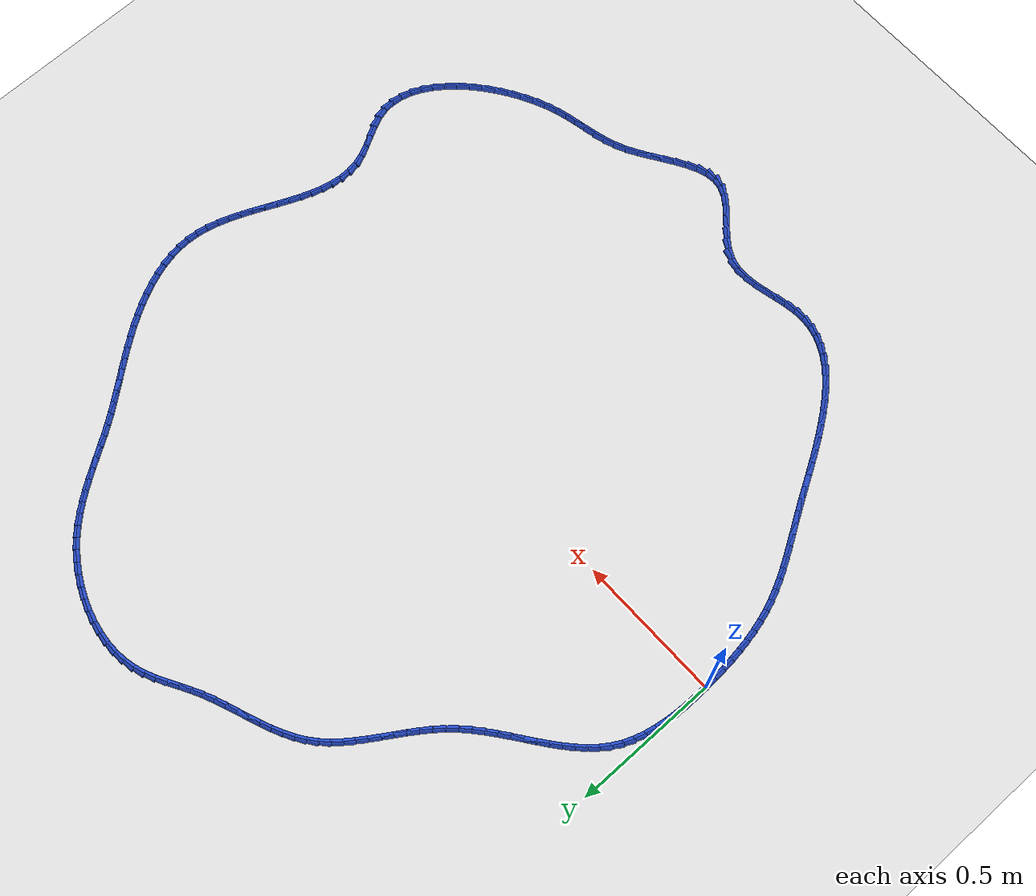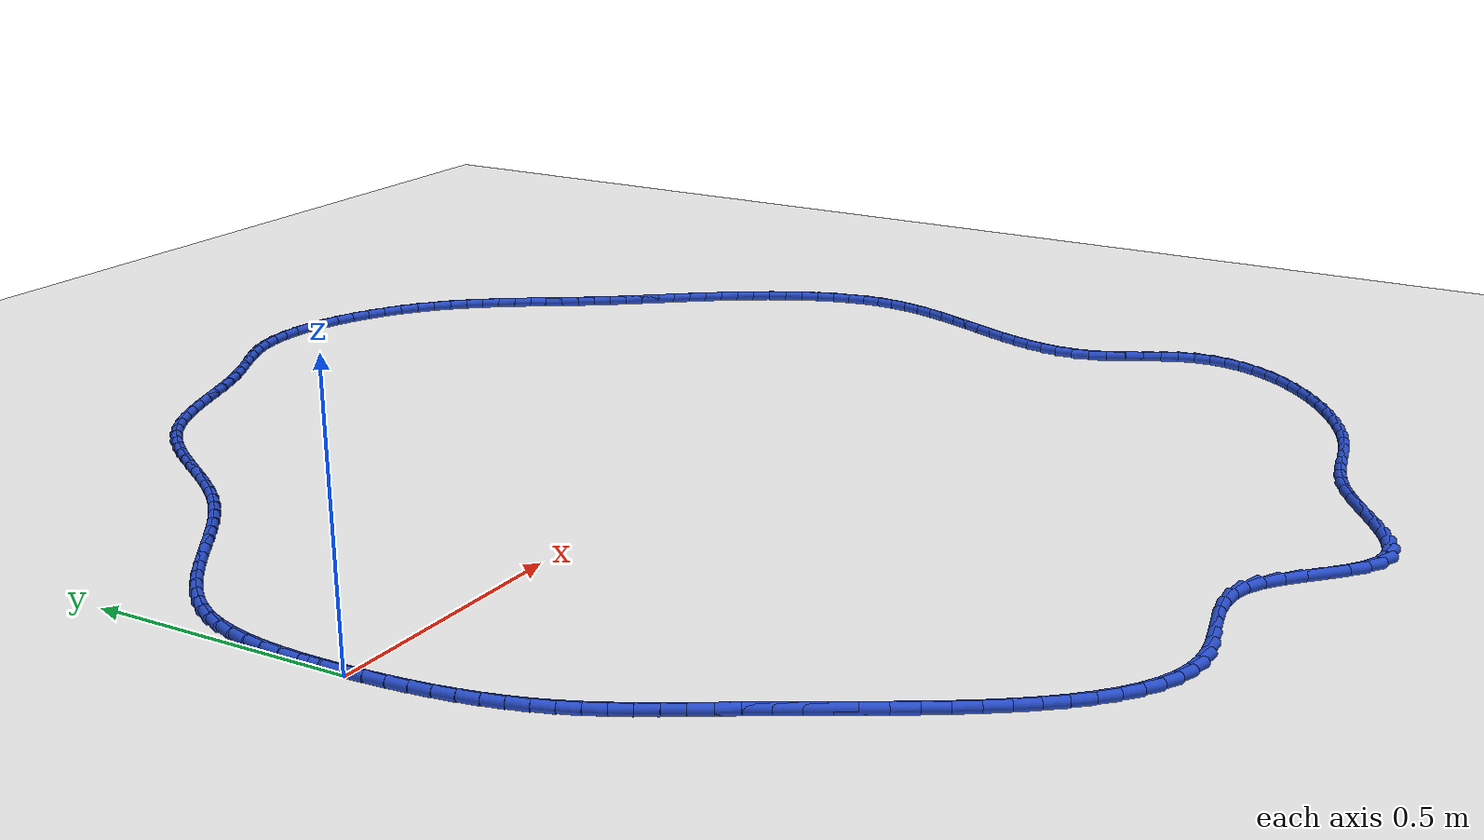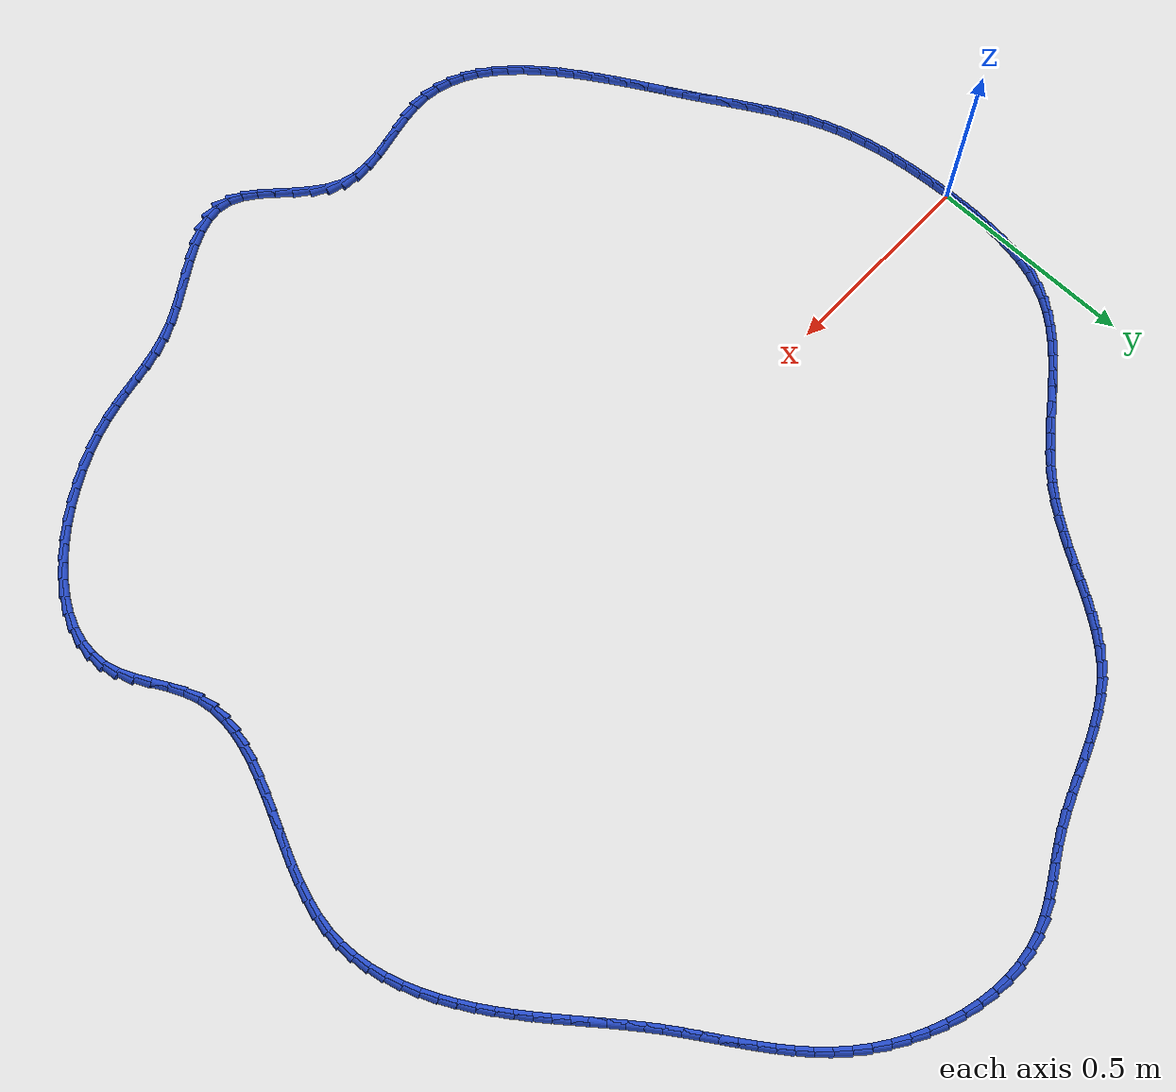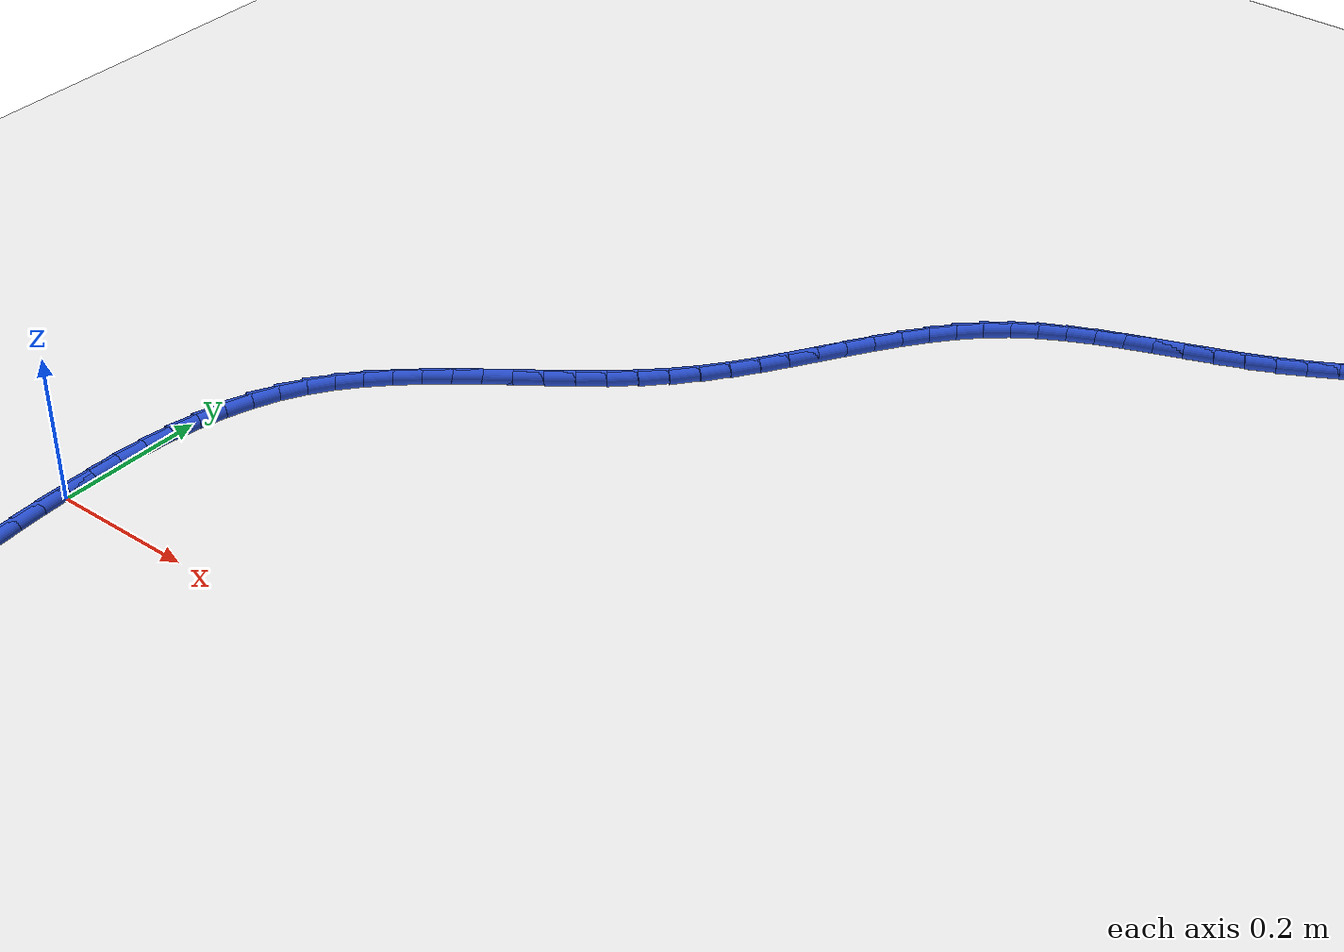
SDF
<sdf version="1.6">
 <world name="default">
  <light name="sun" type="directional">
   <pose>0 0 10 0 -0 0</pose>
   <diffuse>0.8 0.8 0.8 1</diffuse>
   <specular>0.2 0.2 0.2 1</specular>
   <attenuation>
    <range>1000</range>
    <constant>0.9</constant>
    <linear>0.01</linear>
    <quadratic>0.001</quadratic>
   </attenuation>
   <direction>-0.5 0.1 -0.9</direction>
  </light>
  <model name="ground_plane">
   <static>1</static>
   <link name="link">
    <collision name="collision">
     <geometry><plane><normal>0 0 1</normal><size>100 100</size></plane></geometry>
     <surface><friction><ode><mu>100</mu><mu2>50</mu2></ode></friction></surface>
    </collision>
    <visual name="visual">
     <cast_shadows>0</cast_shadows>
     <geometry><plane><normal>0 0 1</normal><size>100 100</size></plane></geometry>
     <material>
      <script><uri>file://media/materials/scripts/gazebo.material</uri><name>Gazebo/WhiteGlow</name></script>
     </material>
    </visual>
   </link>
  </model>
  <gravity>0 0 -9.8</gravity>
  <magnetic_field>6e-06 2.3e-05 -4.2e-05</magnetic_field>
  <atmosphere type="adiabatic"/>
  <physics name="default_physics" default="0" type="ode">
   <max_step_size>0.001</max_step_size>
   <real_time_factor>1</real_time_factor>
   <real_time_update_rate>1000</real_time_update_rate>
  </physics>
  <scene><ambient>0.4 0.4 0.4 1</ambient><background>0.7 0.7 0.7 1</background><shadows>1</shadows></scene>
  <spherical_coordinates>
   <surface_model>EARTH_WGS84</surface_model>
   <latitude_deg>0</latitude_deg>
   <longitude_deg>0</longitude_deg>
   <elevation>0</elevation>
   <heading_deg>0</heading_deg>
  </spherical_coordinates>
  <model name="line">
   <link name="link_0">
    <pose>8.239936510889834e-18 6.938893903907228e-18 0.01 0 1.57 -1.5526000872879415</pose>
    <collision name="collision">
     <geometry><cylinder><radius>0.01</radius><length>0.08</length></cylinder></geometry>
    </collision>
    <visual name="visual">
     <material>
      <script><name>Gazebo/Blue</name><uri>file://media/materials/scripts/gazebo.material</uri></script>
     </material>
     <geometry><cylinder><radius>0.01</radius><length>0.08</length></cylinder></geometry>
    </visual>
   </link>
   <link name="link_1">
    <pose>-0.000732652734478924 0.04025952017222592 0.01 0 1.57 1.5597687728267733</pose>
    <collision name="collision">
     <geometry><cylinder><radius>0.01</radius><length>0.08</length></cylinder></geometry>
    </collision>
    <visual name="visual">
     <material>
      <script><name>Gazebo/Blue</name><uri>file://media/materials/scripts/gazebo.material</uri></script>
     </material>
     <geometry><cylinder><radius>0.01</radius><length>0.08</length></cylinder></geometry>
    </visual>
   </link>
   <link name="link_2">
    <pose>-0.0002883550283096901 0.08054766543197024 0.01 0 1.57 1.5225612813790046</pose>
    <collision name="collision">
     <geometry><cylinder><radius>0.01</radius><length>0.08</length></cylinder></geometry>
    </collision>
    <visual name="visual">
     <material>
      <script><name>Gazebo/Blue</name><uri>file://media/materials/scripts/gazebo.material</uri></script>
     </material>
     <geometry><cylinder><radius>0.01</radius><length>0.08</length></cylinder></geometry>
    </visual>
   </link>
   <link name="link_3">
    <pose>0.0016430891256004592 0.12055894753888144 0.01 0 1.57 1.4765069372273887</pose>
    <collision name="collision">
     <geometry><cylinder><radius>0.01</radius><length>0.08</length></cylinder></geometry>
    </collision>
    <visual name="visual">
     <material>
      <script><name>Gazebo/Blue</name><uri>file://media/materials/scripts/gazebo.material</uri></script>
     </material>
     <geometry><cylinder><radius>0.01</radius><length>0.08</length></cylinder></geometry>
    </visual>
   </link>
   <link name="link_4">
    <pose>0.005371875734344265 0.1599878782526079 0.01 0 1.57 1.4205069318251253</pose>
    <collision name="collision">
     <geometry><cylinder><radius>0.01</radius><length>0.08</length></cylinder></geometry>
    </collision>
    <visual name="visual">
     <material>
      <script><name>Gazebo/Blue</name><uri>file://media/materials/scripts/gazebo.material</uri></script>
     </material>
     <geometry><cylinder><radius>0.01</radius><length>0.08</length></cylinder></geometry>
    </visual>
   </link>
   <link name="link_5">
    <pose>0.01120820080501447 0.19852896933279812 0.01 0 1.57 1.3532871832848776</pose>
    <collision name="collision">
     <geometry><cylinder><radius>0.01</radius><length>0.08</length></cylinder></geometry>
    </collision>
    <visual name="visual">
     <material>
      <script><name>Gazebo/Blue</name><uri>file://media/materials/scripts/gazebo.material</uri></script>
     </material>
     <geometry><cylinder><radius>0.01</radius><length>0.08</length></cylinder></geometry>
    </visual>
   </link>
   <link name="link_6">
    <pose>0.01946226034470383 0.2358767325391006 0.01 0 1.57 1.273532614765716</pose>
    <collision name="collision">
     <geometry><cylinder><radius>0.01</radius><length>0.08</length></cylinder></geometry>
    </collision>
    <visual name="visual">
     <material>
      <script><name>Gazebo/Blue</name><uri>file://media/materials/scripts/gazebo.material</uri></script>
     </material>
     <geometry><cylinder><radius>0.01</radius><length>0.08</length></cylinder></geometry>
    </visual>
   </link>
   <link name="link_7">
    <pose>0.030444250360505055 0.2717256796311635 0.01 0 1.57 1.180145729644687</pose>
    <collision name="collision">
     <geometry><cylinder><radius>0.01</radius><length>0.08</length></cylinder></geometry>
    </collision>
    <visual name="visual">
     <material>
      <script><name>Gazebo/Blue</name><uri>file://media/materials/scripts/gazebo.material</uri></script>
     </material>
     <geometry><cylinder><radius>0.01</radius><length>0.08</length></cylinder></geometry>
    </visual>
   </link>
   <link name="link_8">
    <pose>0.044464366859510954 0.30577032236863555 0.01 0 1.57 1.0729865439448916</pose>
    <collision name="collision">
     <geometry><cylinder><radius>0.01</radius><length>0.08</length></cylinder></geometry>
    </collision>
    <visual name="visual">
     <material>
      <script><name>Gazebo/Blue</name><uri>file://media/materials/scripts/gazebo.material</uri></script>
     </material>
     <geometry><cylinder><radius>0.01</radius><length>0.08</length></cylinder></geometry>
    </visual>
   </link>
   <link name="link_9">
    <pose>0.06182383061221295 0.33771269113031743 0.01 0 1.57 0.9642324731430263</pose>
    <collision name="collision">
     <geometry><cylinder><radius>0.01</radius><length>0.08</length></cylinder></geometry>
    </collision>
    <visual name="visual">
     <material>
      <script><name>Gazebo/Blue</name><uri>file://media/materials/scripts/gazebo.material</uri></script>
     </material>
     <geometry><cylinder><radius>0.01</radius><length>0.08</length></cylinder></geometry>
    </visual>
   </link>
   <link name="link_10">
    <pose>0.08250561355194011 0.3675214155958039 0.01 0 1.57 0.8702356550018028</pose>
    <collision name="collision">
     <geometry><cylinder><radius>0.01</radius><length>0.08</length></cylinder></geometry>
    </collision>
    <visual name="visual">
     <material>
      <script><name>Gazebo/Blue</name><uri>file://media/materials/scripts/gazebo.material</uri></script>
     </material>
     <geometry><cylinder><radius>0.01</radius><length>0.08</length></cylinder></geometry>
    </visual>
   </link>
   <link name="link_11">
    <pose>0.10609618421567167 0.3954972791429456 0.01 0 1.57 0.7930828628265129</pose>
    <collision name="collision">
     <geometry><cylinder><radius>0.01</radius><length>0.08</length></cylinder></geometry>
    </collision>
    <visual name="visual">
     <material>
      <script><name>Gazebo/Blue</name><uri>file://media/materials/scripts/gazebo.material</uri></script>
     </material>
     <geometry><cylinder><radius>0.01</radius><length>0.08</length></cylinder></geometry>
    </visual>
   </link>
   <link name="link_12">
    <pose>0.13215714747092824 0.42196189362127523 0.01 0 1.57 0.7326442263240933</pose>
    <collision name="collision">
     <geometry><cylinder><radius>0.01</radius><length>0.08</length></cylinder></geometry>
    </collision>
    <visual name="visual">
     <material>
      <script><name>Gazebo/Blue</name><uri>file://media/materials/scripts/gazebo.material</uri></script>
     </material>
     <geometry><cylinder><radius>0.01</radius><length>0.08</length></cylinder></geometry>
    </visual>
   </link>
   <link name="link_13">
    <pose>0.16025010818523053 0.44723687088032615 0.01 0 1.57 0.6881047688973753</pose>
    <collision name="collision">
     <geometry><cylinder><radius>0.01</radius><length>0.08</length></cylinder></geometry>
    </collision>
    <visual name="visual">
     <material>
      <script><name>Gazebo/Blue</name><uri>file://media/materials/scripts/gazebo.material</uri></script>
     </material>
     <geometry><cylinder><radius>0.01</radius><length>0.08</length></cylinder></geometry>
    </visual>
   </link>
   <link name="link_14">
    <pose>0.18993667122609909 0.47164382276963107 0.01 0 1.57 0.6584620969948898</pose>
    <collision name="collision">
     <geometry><cylinder><radius>0.01</radius><length>0.08</length></cylinder></geometry>
    </collision>
    <visual name="visual">
     <material>
      <script><name>Gazebo/Blue</name><uri>file://media/materials/scripts/gazebo.material</uri></script>
     </material>
     <geometry><cylinder><radius>0.01</radius><length>0.08</length></cylinder></geometry>
    </visual>
   </link>
   <link name="link_15">
    <pose>0.2207784414610547 0.4955043611387231 0.01 0 1.57 0.6428274807165333</pose>
    <collision name="collision">
     <geometry><cylinder><radius>0.01</radius><length>0.08</length></cylinder></geometry>
    </collision>
    <visual name="visual">
     <material>
      <script><name>Gazebo/Blue</name><uri>file://media/materials/scripts/gazebo.material</uri></script>
     </material>
     <geometry><cylinder><radius>0.01</radius><length>0.08</length></cylinder></geometry>
    </visual>
   </link>
   <link name="link_16">
    <pose>0.252337023757618 0.5191400978371353 0.01 0 1.57 0.6405757938960666</pose>
    <collision name="collision">
     <geometry><cylinder><radius>0.01</radius><length>0.08</length></cylinder></geometry>
    </collision>
    <visual name="visual">
     <material>
      <script><name>Gazebo/Blue</name><uri>file://media/materials/scripts/gazebo.material</uri></script>
     </material>
     <geometry><cylinder><radius>0.01</radius><length>0.08</length></cylinder></geometry>
    </visual>
   </link>
   <link name="link_17">
    <pose>0.2841740229833098 0.5428726447144009 0.01 0 1.57 0.6513981364890858</pose>
    <collision name="collision">
     <geometry><cylinder><radius>0.01</radius><length>0.08</length></cylinder></geometry>
    </collision>
    <visual name="visual">
     <material>
      <script><name>Gazebo/Blue</name><uri>file://media/materials/scripts/gazebo.material</uri></script>
     </material>
     <geometry><cylinder><radius>0.01</radius><length>0.08</length></cylinder></geometry>
    </visual>
   </link>
   <link name="link_18">
    <pose>0.3158510440056504 0.5670236136200524 0.01 0 1.57 0.6752917136091555</pose>
    <collision name="collision">
     <geometry><cylinder><radius>0.01</radius><length>0.08</length></cylinder></geometry>
    </collision>
    <visual name="visual">
     <material>
      <script><name>Gazebo/Blue</name><uri>file://media/materials/scripts/gazebo.material</uri></script>
     </material>
     <geometry><cylinder><radius>0.01</radius><length>0.08</length></cylinder></geometry>
    </visual>
   </link>
   <link name="link_19">
    <pose>0.34692969169216065 0.5919146164036231 0.01 0 1.57 0.7124984638168886</pose>
    <collision name="collision">
     <geometry><cylinder><radius>0.01</radius><length>0.08</length></cylinder></geometry>
    </collision>
    <visual name="visual">
     <material>
      <script><name>Gazebo/Blue</name><uri>file://media/materials/scripts/gazebo.material</uri></script>
     </material>
     <geometry><cylinder><radius>0.01</radius><length>0.08</length></cylinder></geometry>
    </visual>
   </link>
   <link name="link_20">
    <pose>0.37697157091036126 0.6178672649146462 0.01 0 1.57 0.7633846929806167</pose>
    <collision name="collision">
     <geometry><cylinder><radius>0.01</radius><length>0.08</length></cylinder></geometry>
    </collision>
    <visual name="visual">
     <material>
      <script><name>Gazebo/Blue</name><uri>file://media/materials/scripts/gazebo.material</uri></script>
     </material>
     <geometry><cylinder><radius>0.01</radius><length>0.08</length></cylinder></geometry>
    </visual>
   </link>
   <link name="link_21">
    <pose>0.4055382865277729 0.6452031710026542 0.01 0 1.57 0.8278383300147236</pose>
    <collision name="collision">
     <geometry><cylinder><radius>0.01</radius><length>0.08</length></cylinder></geometry>
    </collision>
    <visual name="visual">
     <material>
      <script><name>Gazebo/Blue</name><uri>file://media/materials/scripts/gazebo.material</uri></script>
     </material>
     <geometry><cylinder><radius>0.01</radius><length>0.08</length></cylinder></geometry>
    </visual>
   </link>
   <link name="link_22">
    <pose>0.4322033556187725 0.674233377022473 0.01 0 1.57 0.8930680956362167</pose>
    <collision name="collision">
     <geometry><cylinder><radius>0.01</radius><length>0.08</length></cylinder></geometry>
    </collision>
    <visual name="visual">
     <material>
      <script><name>Gazebo/Blue</name><uri>file://media/materials/scripts/gazebo.material</uri></script>
     </material>
     <geometry><cylinder><radius>0.01</radius><length>0.08</length></cylinder></geometry>
    </visual>
   </link>
   <link name="link_23">
    <pose>0.4569159327710375 0.704935628673091 0.01 0 1.57 0.9438692397849179</pose>
    <collision name="collision">
     <geometry><cylinder><radius>0.01</radius><length>0.08</length></cylinder></geometry>
    </collision>
    <visual name="visual">
     <material>
      <script><name>Gazebo/Blue</name><uri>file://media/materials/scripts/gazebo.material</uri></script>
     </material>
     <geometry><cylinder><radius>0.01</radius><length>0.08</length></cylinder></geometry>
    </visual>
   </link>
   <link name="link_24">
    <pose>0.4800678327624417 0.7368949069379402 0.01 0 1.57 0.9795064248694407</pose>
    <collision name="collision">
     <geometry><cylinder><radius>0.01</radius><length>0.08</length></cylinder></geometry>
    </collision>
    <visual name="visual">
     <material>
      <script><name>Gazebo/Blue</name><uri>file://media/materials/scripts/gazebo.material</uri></script>
     </material>
     <geometry><cylinder><radius>0.01</radius><length>0.08</length></cylinder></geometry>
    </visual>
   </link>
   <link name="link_25">
    <pose>0.5020763004776527 0.7696736291073912 0.01 0 1.57 1.0002111100952045</pose>
    <collision name="collision">
     <geometry><cylinder><radius>0.01</radius><length>0.08</length></cylinder></geometry>
    </collision>
    <visual name="visual">
     <material>
      <script><name>Gazebo/Blue</name><uri>file://media/materials/scripts/gazebo.material</uri></script>
     </material>
     <geometry><cylinder><radius>0.01</radius><length>0.08</length></cylinder></geometry>
    </visual>
   </link>
   <link name="link_26">
    <pose>0.5233585808013387 0.8028342124718146 0.01 0 1.57 1.0060776420269846</pose>
    <collision name="collision">
     <geometry><cylinder><radius>0.01</radius><length>0.08</length></cylinder></geometry>
    </collision>
    <visual name="visual">
     <material>
      <script><name>Gazebo/Blue</name><uri>file://media/materials/scripts/gazebo.material</uri></script>
     </material>
     <geometry><cylinder><radius>0.01</radius><length>0.08</length></cylinder></geometry>
    </visual>
   </link>
   <link name="link_27">
    <pose>0.5443319186181679 0.8359390743215817 0.01 0 1.57 0.996922951426211</pose>
    <collision name="collision">
     <geometry><cylinder><radius>0.01</radius><length>0.08</length></cylinder></geometry>
    </collision>
    <visual name="visual">
     <material>
      <script><name>Gazebo/Blue</name><uri>file://media/materials/scripts/gazebo.material</uri></script>
     </material>
     <geometry><cylinder><radius>0.01</radius><length>0.08</length></cylinder></geometry>
    </visual>
   </link>
   <link name="link_28">
    <pose>0.5654135588128079 0.868550631947063 0.01 0 1.57 0.9722324267450336</pose>
    <collision name="collision">
     <geometry><cylinder><radius>0.01</radius><length>0.08</length></cylinder></geometry>
    </collision>
    <visual name="visual">
     <material>
      <script><name>Gazebo/Blue</name><uri>file://media/materials/scripts/gazebo.material</uri></script>
     </material>
     <geometry><cylinder><radius>0.01</radius><length>0.08</length></cylinder></geometry>
    </visual>
   </link>
   <link name="link_29">
    <pose>0.5870207462699271 0.9002313026386292 0.01 0 1.57 0.9311950903910811</pose>
    <collision name="collision">
     <geometry><cylinder><radius>0.01</radius><length>0.08</length></cylinder></geometry>
    </collision>
    <visual name="visual">
     <material>
      <script><name>Gazebo/Blue</name><uri>file://media/materials/scripts/gazebo.material</uri></script>
     </material>
     <geometry><cylinder><radius>0.01</radius><length>0.08</length></cylinder></geometry>
    </visual>
   </link>
   <link name="link_30">
    <pose>0.6095707258741935 0.9305435036866514 0.01 0 1.57 0.8728598577937738</pose>
    <collision name="collision">
     <geometry><cylinder><radius>0.01</radius><length>0.08</length></cylinder></geometry>
    </collision>
    <visual name="visual">
     <material>
      <script><name>Gazebo/Blue</name><uri>file://media/materials/scripts/gazebo.material</uri></script>
     </material>
     <geometry><cylinder><radius>0.01</radius><length>0.08</length></cylinder></geometry>
    </visual>
   </link>
   <link name="link_31">
    <pose>0.6334807425102751 0.9590496523815005 0.01 0 1.57 0.7964702260245554</pose>
    <collision name="collision">
     <geometry><cylinder><radius>0.01</radius><length>0.08</length></cylinder></geometry>
    </collision>
    <visual name="visual">
     <material>
      <script><name>Gazebo/Blue</name><uri>file://media/materials/scripts/gazebo.material</uri></script>
     </material>
     <geometry><cylinder><radius>0.01</radius><length>0.08</length></cylinder></geometry>
    </visual>
   </link>
   <link name="link_32">
    <pose>0.6591680410628399 0.9853121660135469 0.01 0 1.57 0.7021201968491213</pose>
    <collision name="collision">
     <geometry><cylinder><radius>0.01</radius><length>0.08</length></cylinder></geometry>
    </collision>
    <visual name="visual">
     <material>
      <script><name>Gazebo/Blue</name><uri>file://media/materials/scripts/gazebo.material</uri></script>
     </material>
     <geometry><cylinder><radius>0.01</radius><length>0.08</length></cylinder></geometry>
    </visual>
   </link>
   <link name="link_33">
    <pose>0.6870476698896798 1.0088960804382134 0.01 0 1.57 0.6019573544841942</pose>
    <collision name="collision">
     <geometry><cylinder><radius>0.01</radius><length>0.08</length></cylinder></geometry>
    </collision>
    <visual name="visual">
     <material>
      <script><name>Gazebo/Blue</name><uri>file://media/materials/scripts/gazebo.material</uri></script>
     </material>
     <geometry><cylinder><radius>0.01</radius><length>0.08</length></cylinder></geometry>
    </visual>
   </link>
   <link name="link_34">
    <pose>0.7172820878485096 1.0296675532702149 0.01 0 1.57 0.5182780320993075</pose>
    <collision name="collision">
     <geometry><cylinder><radius>0.01</radius><length>0.08</length></cylinder></geometry>
    </collision>
    <visual name="visual">
     <material>
      <script><name>Gazebo/Blue</name><uri>file://media/materials/scripts/gazebo.material</uri></script>
     </material>
     <geometry><cylinder><radius>0.01</radius><length>0.08</length></cylinder></geometry>
    </visual>
   </link>
   <link name="link_35">
    <pose>0.7495501264799859 1.048069293043882 0.01 0 1.57 0.45362031994810936</pose>
    <collision name="collision">
     <geometry><cylinder><radius>0.01</radius><length>0.08</length></cylinder></geometry>
    </collision>
    <visual name="visual">
     <material>
      <script><name>Gazebo/Blue</name><uri>file://media/materials/scripts/gazebo.material</uri></script>
     </material>
     <geometry><cylinder><radius>0.01</radius><length>0.08</length></cylinder></geometry>
    </visual>
   </link>
   <link name="link_36">
    <pose>0.7834760079723582 1.064609110224804 0.01 0 1.57 0.40720707753410135</pose>
    <collision name="collision">
     <geometry><cylinder><radius>0.01</radius><length>0.08</length></cylinder></geometry>
    </collision>
    <visual name="visual">
     <material>
      <script><name>Gazebo/Blue</name><uri>file://media/materials/scripts/gazebo.material</uri></script>
     </material>
     <geometry><cylinder><radius>0.01</radius><length>0.08</length></cylinder></geometry>
    </visual>
   </link>
   <link name="link_37">
    <pose>0.8186839545138754 1.0797948152785708 0.01 0 1.57 0.3779665944797252</pose>
    <collision name="collision">
     <geometry><cylinder><radius>0.01</radius><length>0.08</length></cylinder></geometry>
    </collision>
    <visual name="visual">
     <material>
      <script><name>Gazebo/Blue</name><uri>file://media/materials/scripts/gazebo.material</uri></script>
     </material>
     <geometry><cylinder><radius>0.01</radius><length>0.08</length></cylinder></geometry>
    </visual>
   </link>
   <link name="link_38">
    <pose>0.8547981882927865 1.0941342186707719 0.01 0 1.57 0.36495588718181465</pose>
    <collision name="collision">
     <geometry><cylinder><radius>0.01</radius><length>0.08</length></cylinder></geometry>
    </collision>
    <visual name="visual">
     <material>
      <script><name>Gazebo/Blue</name><uri>file://media/materials/scripts/gazebo.material</uri></script>
     </material>
     <geometry><cylinder><radius>0.01</radius><length>0.08</length></cylinder></geometry>
    </visual>
   </link>
   <link name="link_39">
    <pose>0.8914429314973411 1.1081351308669973 0.01 0 1.57 0.3675664367834767</pose>
    <collision name="collision">
     <geometry><cylinder><radius>0.01</radius><length>0.08</length></cylinder></geometry>
    </collision>
    <visual name="visual">
     <material>
      <script><name>Gazebo/Blue</name><uri>file://media/materials/scripts/gazebo.material</uri></script>
     </material>
     <geometry><cylinder><radius>0.01</radius><length>0.08</length></cylinder></geometry>
    </visual>
   </link>
   <link name="link_40">
    <pose>0.9282424063157878 1.1223053623328365 0.01 0 1.57 0.38558636863311446</pose>
    <collision name="collision">
     <geometry><cylinder><radius>0.01</radius><length>0.08</length></cylinder></geometry>
    </collision>
    <visual name="visual">
     <material>
      <script><name>Gazebo/Blue</name><uri>file://media/materials/scripts/gazebo.material</uri></script>
     </material>
     <geometry><cylinder><radius>0.01</radius><length>0.08</length></cylinder></geometry>
    </visual>
   </link>
   <link name="link_41">
    <pose>0.9648208349363763 1.1371527235338792 0.01 0 1.57 0.4191633197868349</pose>
    <collision name="collision">
     <geometry><cylinder><radius>0.01</radius><length>0.08</length></cylinder></geometry>
    </collision>
    <visual name="visual">
     <material>
      <script><name>Gazebo/Blue</name><uri>file://media/materials/scripts/gazebo.material</uri></script>
     </material>
     <geometry><cylinder><radius>0.01</radius><length>0.08</length></cylinder></geometry>
    </visual>
   </link>
   <link name="link_42">
    <pose>1.0008024395473547 1.1531850249357147 0.01 0 1.57 0.46791008611691043</pose>
    <collision name="collision">
     <geometry><cylinder><radius>0.01</radius><length>0.08</length></cylinder></geometry>
    </collision>
    <visual name="visual">
     <material>
      <script><name>Gazebo/Blue</name><uri>file://media/materials/scripts/gazebo.material</uri></script>
     </material>
     <geometry><cylinder><radius>0.01</radius><length>0.08</length></cylinder></geometry>
    </visual>
   </link>
   <link name="link_43">
    <pose>1.0358251735515824 1.1708833961236986 0.01 0 1.57 0.510176439108887</pose>
    <collision name="collision">
     <geometry><cylinder><radius>0.01</radius><length>0.08</length></cylinder></geometry>
    </collision>
    <visual name="visual">
     <material>
      <script><name>Gazebo/Blue</name><uri>file://media/materials/scripts/gazebo.material</uri></script>
     </material>
     <geometry><cylinder><radius>0.01</radius><length>0.08</length></cylinder></geometry>
    </visual>
   </link>
   <link name="link_44">
    <pose>1.0699211122101409 1.1899631554715573 0.01 0 1.57 0.5211549498853854</pose>
    <collision name="collision">
     <geometry><cylinder><radius>0.01</radius><length>0.08</length></cylinder></geometry>
    </collision>
    <visual name="visual">
     <material>
      <script><name>Gazebo/Blue</name><uri>file://media/materials/scripts/gazebo.material</uri></script>
     </material>
     <geometry><cylinder><radius>0.01</radius><length>0.08</length></cylinder></geometry>
    </visual>
   </link>
   <link name="link_45">
    <pose>1.1035655909958189 1.209278330275871 0.01 0 1.57 0.49891949203438674</pose>
    <collision name="collision">
     <geometry><cylinder><radius>0.01</radius><length>0.08</length></cylinder></geometry>
    </collision>
    <visual name="visual">
     <material>
      <script><name>Gazebo/Blue</name><uri>file://media/materials/scripts/gazebo.material</uri></script>
     </material>
     <geometry><cylinder><radius>0.01</radius><length>0.08</length></cylinder></geometry>
    </visual>
   </link>
   <link name="link_46">
    <pose>1.1372575468178663 1.2276370882994905 0.01 0 1.57 0.4421913343777353</pose>
    <collision name="collision">
     <geometry><cylinder><radius>0.01</radius><length>0.08</length></cylinder></geometry>
    </collision>
    <visual name="visual">
     <material>
      <script><name>Gazebo/Blue</name><uri>file://media/materials/scripts/gazebo.material</uri></script>
     </material>
     <geometry><cylinder><radius>0.01</radius><length>0.08</length></cylinder></geometry>
    </visual>
   </link>
   <link name="link_47">
    <pose>1.1714959165855325 1.243847597305266 0.01 0 1.57 0.3497722982154622</pose>
    <collision name="collision">
     <geometry><cylinder><radius>0.01</radius><length>0.08</length></cylinder></geometry>
    </collision>
    <visual name="visual">
     <material>
      <script><name>Gazebo/Blue</name><uri>file://media/materials/scripts/gazebo.material</uri></script>
     </material>
     <geometry><cylinder><radius>0.01</radius><length>0.08</length></cylinder></geometry>
    </visual>
   </link>
   <link name="link_48">
    <pose>1.2067796218252715 1.2567180511964138 0.01 0 1.57 0.23067535957727045</pose>
    <collision name="collision">
     <geometry><cylinder><radius>0.01</radius><length>0.08</length></cylinder></geometry>
    </collision>
    <visual name="visual">
     <material>
      <script><name>Gazebo/Blue</name><uri>file://media/materials/scripts/gazebo.material</uri></script>
     </material>
     <geometry><cylinder><radius>0.01</radius><length>0.08</length></cylinder></geometry>
    </visual>
   </link>
   <link name="link_49">
    <pose>1.2434469630554865 1.2653295911556897 0.01 0 1.57 0.11525048066100527</pose>
    <collision name="collision">
     <geometry><cylinder><radius>0.01</radius><length>0.08</length></cylinder></geometry>
    </collision>
    <visual name="visual">
     <material>
      <script><name>Gazebo/Blue</name><uri>file://media/materials/scripts/gazebo.material</uri></script>
     </material>
     <geometry><cylinder><radius>0.01</radius><length>0.08</length></cylinder></geometry>
    </visual>
   </link>
   <link name="link_50">
    <pose>1.2812796236305266 1.269709231776286 0.01 0 1.57 0.009816476666900477</pose>
    <collision name="collision">
     <geometry><cylinder><radius>0.01</radius><length>0.08</length></cylinder></geometry>
    </collision>
    <visual name="visual">
     <material>
      <script><name>Gazebo/Blue</name><uri>file://media/materials/scripts/gazebo.material</uri></script>
     </material>
     <geometry><cylinder><radius>0.01</radius><length>0.08</length></cylinder></geometry>
    </visual>
   </link>
   <link name="link_51">
    <pose>1.3199387960097917 1.2700887408302244 0.01 0 1.57 -0.08635241356312243</pose>
    <collision name="collision">
     <geometry><cylinder><radius>0.01</radius><length>0.08</length></cylinder></geometry>
    </collision>
    <visual name="visual">
     <material>
      <script><name>Gazebo/Blue</name><uri>file://media/materials/scripts/gazebo.material</uri></script>
     </material>
     <geometry><cylinder><radius>0.01</radius><length>0.08</length></cylinder></geometry>
    </visual>
   </link>
   <link name="link_52">
    <pose>1.3590856726526825 1.2666998860895282 0.01 0 1.57 -0.17444766923385047</pose>
    <collision name="collision">
     <geometry><cylinder><radius>0.01</radius><length>0.08</length></cylinder></geometry>
    </collision>
    <visual name="visual">
     <material>
      <script><name>Gazebo/Blue</name><uri>file://media/materials/scripts/gazebo.material</uri></script>
     </material>
     <geometry><cylinder><radius>0.01</radius><length>0.08</length></cylinder></geometry>
    </visual>
   </link>
   <link name="link_53">
    <pose>1.3983814460185984 1.259774435326218 0.01 0 1.57 -0.2558705989483674</pose>
    <collision name="collision">
     <geometry><cylinder><radius>0.01</radius><length>0.08</length></cylinder></geometry>
    </collision>
    <visual name="visual">
     <material>
      <script><name>Gazebo/Blue</name><uri>file://media/materials/scripts/gazebo.material</uri></script>
     </material>
     <geometry><cylinder><radius>0.01</radius><length>0.08</length></cylinder></geometry>
    </visual>
   </link>
   <link name="link_54">
    <pose>1.437487308566941 1.2495441563123164 0.01 0 1.57 -0.3320797615012355</pose>
    <collision name="collision">
     <geometry><cylinder><radius>0.01</radius><length>0.08</length></cylinder></geometry>
    </collision>
    <visual name="visual">
     <material>
      <script><name>Gazebo/Blue</name><uri>file://media/materials/scripts/gazebo.material</uri></script>
     </material>
     <geometry><cylinder><radius>0.01</radius><length>0.08</length></cylinder></geometry>
    </visual>
   </link>
   <link name="link_55">
    <pose>1.4760644527571107 1.236240816819846 0.01 0 1.57 -0.4045190941619599</pose>
    <collision name="collision">
     <geometry><cylinder><radius>0.01</radius><length>0.08</length></cylinder></geometry>
    </collision>
    <visual name="visual">
     <material>
      <script><name>Gazebo/Blue</name><uri>file://media/materials/scripts/gazebo.material</uri></script>
     </material>
     <geometry><cylinder><radius>0.01</radius><length>0.08</length></cylinder></geometry>
    </visual>
   </link>
   <link name="link_56">
    <pose>1.5137740710485073 1.2200961846208285 0.01 0 1.57 -0.47459988961286836</pose>
    <collision name="collision">
     <geometry><cylinder><radius>0.01</radius><length>0.08</length></cylinder></geometry>
    </collision>
    <visual name="visual">
     <material>
      <script><name>Gazebo/Blue</name><uri>file://media/materials/scripts/gazebo.material</uri></script>
     </material>
     <geometry><cylinder><radius>0.01</radius><length>0.08</length></cylinder></geometry>
    </visual>
   </link>
   <link name="link_57">
    <pose>1.5502773559005314 1.2013420274872861 0.01 0 1.57 -0.5437158128022382</pose>
    <collision name="collision">
     <geometry><cylinder><radius>0.01</radius><length>0.08</length></cylinder></geometry>
    </collision>
    <visual name="visual">
     <material>
      <script><name>Gazebo/Blue</name><uri>file://media/materials/scripts/gazebo.material</uri></script>
     </material>
     <geometry><cylinder><radius>0.01</radius><length>0.08</length></cylinder></geometry>
    </visual>
   </link>
   <link name="link_58">
    <pose>1.5852354997725835 1.1802101131912401 0.01 0 1.57 -0.6132775121483026</pose>
    <collision name="collision">
     <geometry><cylinder><radius>0.01</radius><length>0.08</length></cylinder></geometry>
    </collision>
    <visual name="visual">
     <material>
      <script><name>Gazebo/Blue</name><uri>file://media/materials/scripts/gazebo.material</uri></script>
     </material>
     <geometry><cylinder><radius>0.01</radius><length>0.08</length></cylinder></geometry>
    </visual>
   </link>
   <link name="link_59">
    <pose>1.6183096951240639 1.1569322095047145 0.01 0 1.57 -0.6847044109048276</pose>
    <collision name="collision">
     <geometry><cylinder><radius>0.01</radius><length>0.08</length></cylinder></geometry>
    </collision>
    <visual name="visual">
     <material>
      <script><name>Gazebo/Blue</name><uri>file://media/materials/scripts/gazebo.material</uri></script>
     </material>
     <geometry><cylinder><radius>0.01</radius><length>0.08</length></cylinder></geometry>
    </visual>
   </link>
   <link name="link_60">
    <pose>1.6491645330427906 1.1317401005094236 0.01 0 1.57 -0.7554290626280827</pose>
    <collision name="collision">
     <geometry><cylinder><radius>0.01</radius><length>0.08</length></cylinder></geometry>
    </collision>
    <visual name="visual">
     <material>
      <script><name>Gazebo/Blue</name><uri>file://media/materials/scripts/gazebo.material</uri></script>
     </material>
     <geometry><cylinder><radius>0.01</radius><length>0.08</length></cylinder></geometry>
    </visual>
   </link>
   <link name="link_61">
    <pose>1.6776989588125966 1.1048666949305959 0.01 0 1.57 -0.8186812039620099</pose>
    <collision name="collision">
     <geometry><cylinder><radius>0.01</radius><length>0.08</length></cylinder></geometry>
    </collision>
    <visual name="visual">
     <material>
      <script><name>Gazebo/Blue</name><uri>file://media/materials/scripts/gazebo.material</uri></script>
     </material>
     <geometry><cylinder><radius>0.01</radius><length>0.08</length></cylinder></geometry>
    </visual>
   </link>
   <link name="link_62">
    <pose>1.7041938408388853 1.0765467343062143 0.01 0 1.57 -0.8728358423089139</pose>
    <collision name="collision">
     <geometry><cylinder><radius>0.01</radius><length>0.08</length></cylinder></geometry>
    </collision>
    <visual name="visual">
     <material>
      <script><name>Gazebo/Blue</name><uri>file://media/materials/scripts/gazebo.material</uri></script>
     </material>
     <geometry><cylinder><radius>0.01</radius><length>0.08</length></cylinder></geometry>
    </visual>
   </link>
   <link name="link_63">
    <pose>1.7289651850000305 1.047015128795655 0.01 0 1.57 -0.9172488155020763</pose>
    <collision name="collision">
     <geometry><cylinder><radius>0.01</radius><length>0.08</length></cylinder></geometry>
    </collision>
    <visual name="visual">
     <material>
      <script><name>Gazebo/Blue</name><uri>file://media/materials/scripts/gazebo.material</uri></script>
     </material>
     <geometry><cylinder><radius>0.01</radius><length>0.08</length></cylinder></geometry>
    </visual>
   </link>
   <link name="link_64">
    <pose>1.7523289971744072 1.0165067885582937 0.01 0 1.57 -0.9515913978916665</pose>
    <collision name="collision">
     <geometry><cylinder><radius>0.01</radius><length>0.08</length></cylinder></geometry>
    </collision>
    <visual name="visual">
     <material>
      <script><name>Gazebo/Blue</name><uri>file://media/materials/scripts/gazebo.material</uri></script>
     </material>
     <geometry><cylinder><radius>0.01</radius><length>0.08</length></cylinder></geometry>
    </visual>
   </link>
   <link name="link_65">
    <pose>1.7746012832403901 0.985256623753507 0.01 0 1.57 -0.975733914231562</pose>
    <collision name="collision">
     <geometry><cylinder><radius>0.01</radius><length>0.08</length></cylinder></geometry>
    </collision>
    <visual name="visual">
     <material>
      <script><name>Gazebo/Blue</name><uri>file://media/materials/scripts/gazebo.material</uri></script>
     </material>
     <geometry><cylinder><radius>0.01</radius><length>0.08</length></cylinder></geometry>
    </visual>
   </link>
   <link name="link_66">
    <pose>1.7960980490763516 0.953499544540671 0.01 0 1.57 -0.9896436483872656</pose>
    <collision name="collision">
     <geometry><cylinder><radius>0.01</radius><length>0.08</length></cylinder></geometry>
    </collision>
    <visual name="visual">
     <material>
      <script><name>Gazebo/Blue</name><uri>file://media/materials/scripts/gazebo.material</uri></script>
     </material>
     <geometry><cylinder><radius>0.01</radius><length>0.08</length></cylinder></geometry>
    </visual>
   </link>
   <link name="link_67">
    <pose>1.8171353005606667 0.9214704610791613 0.01 0 1.57 -0.9933098073378793</pose>
    <collision name="collision">
     <geometry><cylinder><radius>0.01</radius><length>0.08</length></cylinder></geometry>
    </collision>
    <visual name="visual">
     <material>
      <script><name>Gazebo/Blue</name><uri>file://media/materials/scripts/gazebo.material</uri></script>
     </material>
     <geometry><cylinder><radius>0.01</radius><length>0.08</length></cylinder></geometry>
    </visual>
   </link>
   <link name="link_68">
    <pose>1.83802904357171 0.8894042835283544 0.01 0 1.57 -0.9866996945480181</pose>
    <collision name="collision">
     <geometry><cylinder><radius>0.01</radius><length>0.08</length></cylinder></geometry>
    </collision>
    <visual name="visual">
     <material>
      <script><name>Gazebo/Blue</name><uri>file://media/materials/scripts/gazebo.material</uri></script>
     </material>
     <geometry><cylinder><radius>0.01</radius><length>0.08</length></cylinder></geometry>
    </visual>
   </link>
   <link name="link_69">
    <pose>1.8590952839878554 0.8575359220476265 0.01 0 1.57 -0.969746816540052</pose>
    <collision name="collision">
     <geometry><cylinder><radius>0.01</radius><length>0.08</length></cylinder></geometry>
    </collision>
    <visual name="visual">
     <material>
      <script><name>Gazebo/Blue</name><uri>file://media/materials/scripts/gazebo.material</uri></script>
     </material>
     <geometry><cylinder><radius>0.01</radius><length>0.08</length></cylinder></geometry>
    </visual>
   </link>
   <link name="link_70">
    <pose>1.8806500276874765 0.8261002867963538 0.01 0 1.57 -0.9442683324021134</pose>
    <collision name="collision">
     <geometry><cylinder><radius>0.01</radius><length>0.08</length></cylinder></geometry>
    </collision>
    <visual name="visual">
     <material>
      <script><name>Gazebo/Blue</name><uri>file://media/materials/scripts/gazebo.material</uri></script>
     </material>
     <geometry><cylinder><radius>0.01</radius><length>0.08</length></cylinder></geometry>
    </visual>
   </link>
   <link name="link_71">
    <pose>1.9029536798570315 0.795286067098332 0.01 0 1.57 -0.9215701571300232</pose>
    <collision name="collision">
     <geometry><cylinder><radius>0.01</radius><length>0.08</length></cylinder></geometry>
    </collision>
    <visual name="visual">
     <material>
      <script><name>Gazebo/Blue</name><uri>file://media/materials/scripts/gazebo.material</uri></script>
     </material>
     <geometry><cylinder><radius>0.01</radius><length>0.08</length></cylinder></geometry>
    </visual>
   </link>
   <link name="link_72">
    <pose>1.9259353525421583 0.7650065484062413 0.01 0 1.57 -0.9059077089990951</pose>
    <collision name="collision">
     <geometry><cylinder><radius>0.01</radius><length>0.08</length></cylinder></geometry>
    </collision>
    <visual name="visual">
     <material>
      <script><name>Gazebo/Blue</name><uri>file://media/materials/scripts/gazebo.material</uri></script>
     </material>
     <geometry><cylinder><radius>0.01</radius><length>0.08</length></cylinder></geometry>
    </visual>
   </link>
   <link name="link_73">
    <pose>1.9494019587494928 0.7350734321547396 0.01 0 1.57 -0.8973238643277884</pose>
    <collision name="collision">
     <geometry><cylinder><radius>0.01</radius><length>0.08</length></cylinder></geometry>
    </collision>
    <visual name="visual">
     <material>
      <script><name>Gazebo/Blue</name><uri>file://media/materials/scripts/gazebo.material</uri></script>
     </material>
     <geometry><cylinder><radius>0.01</radius><length>0.08</length></cylinder></geometry>
    </visual>
   </link>
   <link name="link_74">
    <pose>1.9731602183554142 0.7052982592293683 0.01 0 1.57 -0.8958082652464978</pose>
    <collision name="collision">
     <geometry><cylinder><radius>0.01</radius><length>0.08</length></cylinder></geometry>
    </collision>
    <visual name="visual">
     <material>
      <script><name>Gazebo/Blue</name><uri>file://media/materials/scripts/gazebo.material</uri></script>
     </material>
     <geometry><cylinder><radius>0.01</radius><length>0.08</length></cylinder></geometry>
    </visual>
   </link>
   <link name="link_75">
    <pose>1.9970168512362996 0.675492570515669 0.01 0 1.57 -0.9013170855567493</pose>
    <collision name="collision">
     <geometry><cylinder><radius>0.01</radius><length>0.08</length></cylinder></geometry>
    </collision>
    <visual name="visual">
     <material>
      <script><name>Gazebo/Blue</name><uri>file://media/materials/scripts/gazebo.material</uri></script>
     </material>
     <geometry><cylinder><radius>0.01</radius><length>0.08</length></cylinder></geometry>
    </visual>
   </link>
   <link name="link_76">
    <pose>2.020778577268526 0.6454679068991833 0.01 0 1.57 -0.913775996135123</pose>
    <collision name="collision">
     <geometry><cylinder><radius>0.01</radius><length>0.08</length></cylinder></geometry>
    </collision>
    <visual name="visual">
     <material>
      <script><name>Gazebo/Blue</name><uri>file://media/materials/scripts/gazebo.material</uri></script>
     </material>
     <geometry><cylinder><radius>0.01</radius><length>0.08</length></cylinder></geometry>
    </visual>
   </link>
   <link name="link_77">
    <pose>2.0442521163284715 0.6150358092654524 0.01 0 1.57 -0.933073262158163</pose>
    <collision name="collision">
     <geometry><cylinder><radius>0.01</radius><length>0.08</length></cylinder></geometry>
    </collision>
    <visual name="visual">
     <material>
      <script><name>Gazebo/Blue</name><uri>file://media/materials/scripts/gazebo.material</uri></script>
     </material>
     <geometry><cylinder><radius>0.01</radius><length>0.08</length></cylinder></geometry>
    </visual>
   </link>
   <link name="link_78">
    <pose>2.0672441882925137 0.5840078185000179 0.01 0 1.57 -0.9590440071209725</pose>
    <collision name="collision">
     <geometry><cylinder><radius>0.01</radius><length>0.08</length></cylinder></geometry>
    </collision>
    <visual name="visual">
     <material>
      <script><name>Gazebo/Blue</name><uri>file://media/materials/scripts/gazebo.material</uri></script>
     </material>
     <geometry><cylinder><radius>0.01</radius><length>0.08</length></cylinder></geometry>
    </visual>
   </link>
   <link name="link_79">
    <pose>2.08956151303703 0.5521954754884212 0.01 0 1.57 -0.9914472646458061</pose>
    <collision name="collision">
     <geometry><cylinder><radius>0.01</radius><length>0.08</length></cylinder></geometry>
    </collision>
    <visual name="visual">
     <material>
      <script><name>Gazebo/Blue</name><uri>file://media/materials/scripts/gazebo.material</uri></script>
     </material>
     <geometry><cylinder><radius>0.01</radius><length>0.08</length></cylinder></geometry>
    </visual>
   </link>
   <link name="link_80">
    <pose>2.1110107291794407 0.5194104646662899 0.01 0 1.57 -1.029882686592179</pose>
    <collision name="collision">
     <geometry><cylinder><radius>0.01</radius><length>0.08</length></cylinder></geometry>
    </collision>
    <visual name="visual">
     <material>
      <script><name>Gazebo/Blue</name><uri>file://media/materials/scripts/gazebo.material</uri></script>
     </material>
     <geometry><cylinder><radius>0.01</radius><length>0.08</length></cylinder></geometry>
    </visual>
   </link>
   <link name="link_81">
    <pose>2.131354802171431 0.48554162241392873 0.01 0 1.57 -1.0742848455316873</pose>
    <collision name="collision">
     <geometry><cylinder><radius>0.01</radius><length>0.08</length></cylinder></geometry>
    </collision>
    <visual name="visual">
     <material>
      <script><name>Gazebo/Blue</name><uri>file://media/materials/scripts/gazebo.material</uri></script>
     </material>
     <geometry><cylinder><radius>0.01</radius><length>0.08</length></cylinder></geometry>
    </visual>
   </link>
   <link name="link_82">
    <pose>2.1502411026345682 0.4506819921066975 0.01 0 1.57 -1.1253376866484457</pose>
    <collision name="collision">
     <geometry><cylinder><radius>0.01</radius><length>0.08</length></cylinder></geometry>
    </collision>
    <visual name="visual">
     <material>
      <script><name>Gazebo/Blue</name><uri>file://media/materials/scripts/gazebo.material</uri></script>
     </material>
     <geometry><cylinder><radius>0.01</radius><length>0.08</length></cylinder></geometry>
    </visual>
   </link>
   <link name="link_83">
    <pose>2.167298094435765 0.4149580173295469 0.01 0 1.57 -1.1838898248102667</pose>
    <collision name="collision">
     <geometry><cylinder><radius>0.01</radius><length>0.08</length></cylinder></geometry>
    </collision>
    <visual name="visual">
     <material>
      <script><name>Gazebo/Blue</name><uri>file://media/materials/scripts/gazebo.material</uri></script>
     </material>
     <geometry><cylinder><radius>0.01</radius><length>0.08</length></cylinder></geometry>
    </visual>
   </link>
   <link name="link_84">
    <pose>2.182154241441937 0.3784961416674266 0.01 0 1.57 -1.2508435677028216</pose>
    <collision name="collision">
     <geometry><cylinder><radius>0.01</radius><length>0.08</length></cylinder></geometry>
    </collision>
    <visual name="visual">
     <material>
      <script><name>Gazebo/Blue</name><uri>file://media/materials/scripts/gazebo.material</uri></script>
     </material>
     <geometry><cylinder><radius>0.01</radius><length>0.08</length></cylinder></geometry>
    </visual>
   </link>
   <link name="link_85">
    <pose>2.1944380075199965 0.3414228087052875 0.01 0 1.57 -1.3270644298050371</pose>
    <collision name="collision">
     <geometry><cylinder><radius>0.01</radius><length>0.08</length></cylinder></geometry>
    </collision>
    <visual name="visual">
     <material>
      <script><name>Gazebo/Blue</name><uri>file://media/materials/scripts/gazebo.material</uri></script>
     </material>
     <geometry><cylinder><radius>0.01</radius><length>0.08</length></cylinder></geometry>
    </visual>
   </link>
   <link name="link_86">
    <pose>2.2037778565368584 0.30386446202808015 0.01 0 1.57 -1.4132292836774563</pose>
    <collision name="collision">
     <geometry><cylinder><radius>0.01</radius><length>0.08</length></cylinder></geometry>
    </collision>
    <visual name="visual">
     <material>
      <script><name>Gazebo/Blue</name><uri>file://media/materials/scripts/gazebo.material</uri></script>
     </material>
     <geometry><cylinder><radius>0.01</radius><length>0.08</length></cylinder></geometry>
    </visual>
   </link>
   <link name="link_87">
    <pose>2.2098022523594367 0.26594754522075426 0.01 0 1.57 -1.5096024425093275</pose>
    <collision name="collision">
     <geometry><cylinder><radius>0.01</radius><length>0.08</length></cylinder></geometry>
    </collision>
    <visual name="visual">
     <material>
      <script><name>Gazebo/Blue</name><uri>file://media/materials/scripts/gazebo.material</uri></script>
     </material>
     <geometry><cylinder><radius>0.01</radius><length>0.08</length></cylinder></geometry>
    </visual>
   </link>
   <link name="link_88">
    <pose>2.212139658854645 0.22779850186826048 0.01 0 1.57 1.5258990293781916</pose>
    <collision name="collision">
     <geometry><cylinder><radius>0.01</radius><length>0.08</length></cylinder></geometry>
    </collision>
    <visual name="visual">
     <material>
      <script><name>Gazebo/Blue</name><uri>file://media/materials/scripts/gazebo.material</uri></script>
     </material>
     <geometry><cylinder><radius>0.01</radius><length>0.08</length></cylinder></geometry>
    </visual>
   </link>
   <link name="link_89">
    <pose>2.2104209596275686 0.1895435435945242 0.01 0 1.57 1.4197555149696566</pose>
    <collision name="collision">
     <geometry><cylinder><radius>0.01</radius><length>0.08</length></cylinder></geometry>
    </collision>
    <visual name="visual">
     <material>
      <script><name>Gazebo/Blue</name><uri>file://media/materials/scripts/gazebo.material</uri></script>
     </material>
     <geometry><cylinder><radius>0.01</radius><length>0.08</length></cylinder></geometry>
    </visual>
   </link>
   <link name="link_90">
    <pose>2.2045969772404965 0.15127821202398256 0.01 0 1.57 1.3311997230649972</pose>
    <collision name="collision">
     <geometry><cylinder><radius>0.01</radius><length>0.08</length></cylinder></geometry>
    </collision>
    <visual name="visual">
     <material>
      <script><name>Gazebo/Blue</name><uri>file://media/materials/scripts/gazebo.material</uri></script>
     </material>
     <geometry><cylinder><radius>0.01</radius><length>0.08</length></cylinder></geometry>
    </visual>
   </link>
   <link name="link_91">
    <pose>2.1952550696369353 0.1130370292041277 0.01 0 1.57 1.2616524955967945</pose>
    <collision name="collision">
     <geometry><cylinder><radius>0.01</radius><length>0.08</length></cylinder></geometry>
    </collision>
    <visual name="visual">
     <material>
      <script><name>Gazebo/Blue</name><uri>file://media/materials/scripts/gazebo.material</uri></script>
     </material>
     <geometry><cylinder><radius>0.01</radius><length>0.08</length></cylinder></geometry>
    </visual>
   </link>
   <link name="link_92">
    <pose>2.183057890687254 0.07484729916168316 0.01 0 1.57 1.2097689860366725</pose>
    <collision name="collision">
     <geometry><cylinder><radius>0.01</radius><length>0.08</length></cylinder></geometry>
    </collision>
    <visual name="visual">
     <material>
      <script><name>Gazebo/Blue</name><uri>file://media/materials/scripts/gazebo.material</uri></script>
     </material>
     <geometry><cylinder><radius>0.01</radius><length>0.08</length></cylinder></geometry>
    </visual>
   </link>
   <link name="link_93">
    <pose>2.168668094261816 0.036736325923372205 0.01 0 1.57 1.1741149009651564</pose>
    <collision name="collision">
     <geometry><cylinder><radius>0.01</radius><length>0.08</length></cylinder></geometry>
    </collision>
    <visual name="visual">
     <material>
      <script><name>Gazebo/Blue</name><uri>file://media/materials/scripts/gazebo.material</uri></script>
     </material>
     <geometry><cylinder><radius>0.01</radius><length>0.08</length></cylinder></geometry>
    </visual>
   </link>
   <link name="link_94">
    <pose>2.1527483342309903 -0.0012685864840829408 0.01 0 1.57 1.1535586880624649</pose>
    <collision name="collision">
     <geometry><cylinder><radius>0.01</radius><length>0.08</length></cylinder></geometry>
    </collision>
    <visual name="visual">
     <material>
      <script><name>Gazebo/Blue</name><uri>file://media/materials/scripts/gazebo.material</uri></script>
     </material>
     <geometry><cylinder><radius>0.01</radius><length>0.08</length></cylinder></geometry>
    </visual>
   </link>
   <link name="link_95">
    <pose>2.1359612644651413 -0.039140134033958926 0.01 0 1.57 1.1474611043986702</pose>
    <collision name="collision">
     <geometry><cylinder><radius>0.01</radius><length>0.08</length></cylinder></geometry>
    </collision>
    <visual name="visual">
     <material>
      <script><name>Gazebo/Blue</name><uri>file://media/materials/scripts/gazebo.material</uri></script>
     </material>
     <geometry><cylinder><radius>0.01</radius><length>0.08</length></cylinder></geometry>
    </visual>
   </link>
   <link name="link_96">
    <pose>2.118969538834637 -0.07685101269953276 0.01 0 1.57 1.1557615441621376</pose>
    <collision name="collision">
     <geometry><cylinder><radius>0.01</radius><length>0.08</length></cylinder></geometry>
    </collision>
    <visual name="visual">
     <material>
      <script><name>Gazebo/Blue</name><uri>file://media/materials/scripts/gazebo.material</uri></script>
     </material>
     <geometry><cylinder><radius>0.01</radius><length>0.08</length></cylinder></geometry>
    </visual>
   </link>
   <link name="link_97">
    <pose>2.102435811209842 -0.11437391845408149 0.01 0 1.57 1.179018469502335</pose>
    <collision name="collision">
     <geometry><cylinder><radius>0.01</radius><length>0.08</length></cylinder></geometry>
    </collision>
    <visual name="visual">
     <material>
      <script><name>Gazebo/Blue</name><uri>file://media/materials/scripts/gazebo.material</uri></script>
     </material>
     <geometry><cylinder><radius>0.01</radius><length>0.08</length></cylinder></geometry>
    </visual>
   </link>
   <link name="link_98">
    <pose>2.0870227354611246 -0.1516815472708813 0.01 0 1.57 1.218418342335773</pose>
    <collision name="collision">
     <geometry><cylinder><radius>0.01</radius><length>0.08</length></cylinder></geometry>
    </collision>
    <visual name="visual">
     <material>
      <script><name>Gazebo/Blue</name><uri>file://media/materials/scripts/gazebo.material</uri></script>
     </material>
     <geometry><cylinder><radius>0.01</radius><length>0.08</length></cylinder></geometry>
    </visual>
   </link>
   <link name="link_99">
    <pose>2.07339296545885 -0.18874659512321085 0.01 0 1.57 1.2757216048867401</pose>
    <collision name="collision">
     <geometry><cylinder><radius>0.01</radius><length>0.08</length></cylinder></geometry>
    </collision>
    <visual name="visual">
     <material>
      <script><name>Gazebo/Blue</name><uri>file://media/materials/scripts/gazebo.material</uri></script>
     </material>
     <geometry><cylinder><radius>0.01</radius><length>0.08</length></cylinder></geometry>
    </visual>
   </link>
   <link name="link_100">
    <pose>2.0622091550733854 -0.22554175798434636 0.01 0 1.57 1.3530535147793727</pose>
    <collision name="collision">
     <geometry><cylinder><radius>0.01</radius><length>0.08</length></cylinder></geometry>
    </collision>
    <visual name="visual">
     <material>
      <script><name>Gazebo/Blue</name><uri>file://media/materials/scripts/gazebo.material</uri></script>
     </material>
     <geometry><cylinder><radius>0.01</radius><length>0.08</length></cylinder></geometry>
    </visual>
   </link>
   <link name="link_101">
    <pose>2.0541339581750964 -0.26203973182756485 0.01 0 1.57 1.4523728025363662</pose>
    <collision name="collision">
     <geometry><cylinder><radius>0.01</radius><length>0.08</length></cylinder></geometry>
    </collision>
    <visual name="visual">
     <material>
      <script><name>Gazebo/Blue</name><uri>file://media/materials/scripts/gazebo.material</uri></script>
     </material>
     <geometry><cylinder><radius>0.01</radius><length>0.08</length></cylinder></geometry>
    </visual>
   </link>
   <link name="link_102">
    <pose>2.0498300286343496 -0.2982132126261433 0.01 0 1.57 -1.567167487973289</pose>
    <collision name="collision">
     <geometry><cylinder><radius>0.01</radius><length>0.08</length></cylinder></geometry>
    </collision>
    <visual name="visual">
     <material>
      <script><name>Gazebo/Blue</name><uri>file://media/materials/scripts/gazebo.material</uri></script>
     </material>
     <geometry><cylinder><radius>0.01</radius><length>0.08</length></cylinder></geometry>
    </visual>
   </link>
   <link name="link_103">
    <pose>2.049960020321512 -0.33403489635335887 0.01 0 1.57 -1.4243857867227545</pose>
    <collision name="collision">
     <geometry><cylinder><radius>0.01</radius><length>0.08</length></cylinder></geometry>
    </collision>
    <visual name="visual">
     <material>
      <script><name>Gazebo/Blue</name><uri>file://media/materials/scripts/gazebo.material</uri></script>
     </material>
     <geometry><cylinder><radius>0.01</radius><length>0.08</length></cylinder></geometry>
    </visual>
   </link>
   <link name="link_104">
    <pose>2.055186587106949 -0.3694774789824884 0.01 0 1.57 -1.267396346737297</pose>
    <collision name="collision">
     <geometry><cylinder><radius>0.01</radius><length>0.08</length></cylinder></geometry>
    </collision>
    <visual name="visual">
     <material>
      <script><name>Gazebo/Blue</name><uri>file://media/materials/scripts/gazebo.material</uri></script>
     </material>
     <geometry><cylinder><radius>0.01</radius><length>0.08</length></cylinder></geometry>
    </visual>
   </link>
   <link name="link_105">
    <pose>2.066155547434597 -0.40451474784488467 0.01 0 1.57 -1.1351395351754185</pose>
    <collision name="collision">
     <geometry><cylinder><radius>0.01</radius><length>0.08</length></cylinder></geometry>
    </collision>
    <visual name="visual">
     <material>
      <script><name>Gazebo/Blue</name><uri>file://media/materials/scripts/gazebo.material</uri></script>
     </material>
     <geometry><cylinder><radius>0.01</radius><length>0.08</length></cylinder></geometry>
    </visual>
   </link>
   <link name="link_106">
    <pose>2.082300595073131 -0.4391990663661438 0.01 0 1.57 -1.073148735877293</pose>
    <collision name="collision">
     <geometry><cylinder><radius>0.01</radius><length>0.08</length></cylinder></geometry>
    </collision>
    <visual name="visual">
     <material>
      <script><name>Gazebo/Blue</name><uri>file://media/materials/scripts/gazebo.material</uri></script>
     </material>
     <geometry><cylinder><radius>0.01</radius><length>0.08</length></cylinder></geometry>
    </visual>
   </link>
   <link name="link_107">
    <pose>2.10105023884851 -0.473712784271328 0.01 0 1.57 -1.076913587153937</pose>
    <collision name="collision">
     <geometry><cylinder><radius>0.01</radius><length>0.08</length></cylinder></geometry>
    </collision>
    <visual name="visual">
     <material>
      <script><name>Gazebo/Blue</name><uri>file://media/materials/scripts/gazebo.material</uri></script>
     </material>
     <geometry><cylinder><radius>0.01</radius><length>0.08</length></cylinder></geometry>
    </visual>
   </link>
   <link name="link_108">
    <pose>2.1196448307588613 -0.5082504485692757 0.01 0 1.57 -1.1469948027619543</pose>
    <collision name="collision">
     <geometry><cylinder><radius>0.01</radius><length>0.08</length></cylinder></geometry>
    </collision>
    <visual name="visual">
     <material>
      <script><name>Gazebo/Blue</name><uri>file://media/materials/scripts/gazebo.material</uri></script>
     </material>
     <geometry><cylinder><radius>0.01</radius><length>0.08</length></cylinder></geometry>
    </visual>
   </link>
   <link name="link_109">
    <pose>2.135324722802314 -0.5430066062688255 0.01 0 1.57 -1.2924719879193531</pose>
    <collision name="collision">
     <geometry><cylinder><radius>0.01</radius><length>0.08</length></cylinder></geometry>
    </collision>
    <visual name="visual">
     <material>
      <script><name>Gazebo/Blue</name><uri>file://media/materials/scripts/gazebo.material</uri></script>
     </material>
     <geometry><cylinder><radius>0.01</radius><length>0.08</length></cylinder></geometry>
    </visual>
   </link>
   <link name="link_110">
    <pose>2.1453723418731316 -0.5781699876458133 0.01 0 1.57 -1.4833399422382945</pose>
    <collision name="collision">
     <geometry><cylinder><radius>0.01</radius><length>0.08</length></cylinder></geometry>
    </collision>
    <visual name="visual">
     <material>
      <script><name>Gazebo/Blue</name><uri>file://media/materials/scripts/gazebo.material</uri></script>
     </material>
     <geometry><cylinder><radius>0.01</radius><length>0.08</length></cylinder></geometry>
    </visual>
   </link>
   <link name="link_111">
    <pose>2.148490504637371 -0.6137329581880271 0.01 0 1.57 1.4764682847433395</pose>
    <collision name="collision">
     <geometry><cylinder><radius>0.01</radius><length>0.08</length></cylinder></geometry>
    </collision>
    <visual name="visual">
     <material>
      <script><name>Gazebo/Blue</name><uri>file://media/materials/scripts/gazebo.material</uri></script>
     </material>
     <geometry><cylinder><radius>0.01</radius><length>0.08</length></cylinder></geometry>
    </visual>
   </link>
   <link name="link_112">
    <pose>2.145111471984344 -0.6494487927089305 0.01 0 1.57 1.314288769849825</pose>
    <collision name="collision">
     <geometry><cylinder><radius>0.01</radius><length>0.08</length></cylinder></geometry>
    </collision>
    <visual name="visual">
     <material>
      <script><name>Gazebo/Blue</name><uri>file://media/materials/scripts/gazebo.material</uri></script>
     </material>
     <geometry><cylinder><radius>0.01</radius><length>0.08</length></cylinder></geometry>
    </visual>
   </link>
   <link name="link_113">
    <pose>2.135772142533697 -0.6850563001576554 0.01 0 1.57 1.1740667275033256</pose>
    <collision name="collision">
     <geometry><cylinder><radius>0.01</radius><length>0.08</length></cylinder></geometry>
    </collision>
    <visual name="visual">
     <material>
      <script><name>Gazebo/Blue</name><uri>file://media/materials/scripts/gazebo.material</uri></script>
     </material>
     <geometry><cylinder><radius>0.01</radius><length>0.08</length></cylinder></geometry>
    </visual>
   </link>
   <link name="link_114">
    <pose>2.1210094149050764 -0.7202942894833325 0.01 0 1.57 1.0544070582088172</pose>
    <collision name="collision">
     <geometry><cylinder><radius>0.01</radius><length>0.08</length></cylinder></geometry>
    </collision>
    <visual name="visual">
     <material>
      <script><name>Gazebo/Blue</name><uri>file://media/materials/scripts/gazebo.material</uri></script>
     </material>
     <geometry><cylinder><radius>0.01</radius><length>0.08</length></cylinder></geometry>
    </visual>
   </link>
   <link name="link_115">
    <pose>2.1013601877181305 -0.7549015696350925 0.01 0 1.57 0.9521903780876299</pose>
    <collision name="collision">
     <geometry><cylinder><radius>0.01</radius><length>0.08</length></cylinder></geometry>
    </collision>
    <visual name="visual">
     <material>
      <script><name>Gazebo/Blue</name><uri>file://media/materials/scripts/gazebo.material</uri></script>
     </material>
     <geometry><cylinder><radius>0.01</radius><length>0.08</length></cylinder></geometry>
    </visual>
   </link>
   <link name="link_116">
    <pose>2.0773613595925045 -0.7886169495620662 0.01 0 1.57 0.8639253964860568</pose>
    <collision name="collision">
     <geometry><cylinder><radius>0.01</radius><length>0.08</length></cylinder></geometry>
    </collision>
    <visual name="visual">
     <material>
      <script><name>Gazebo/Blue</name><uri>file://media/materials/scripts/gazebo.material</uri></script>
     </material>
     <geometry><cylinder><radius>0.01</radius><length>0.08</length></cylinder></geometry>
    </visual>
   </link>
   <link name="link_117">
    <pose>2.049549829147846 -0.8211792382133845 0.01 0 1.57 0.7863730461742056</pose>
    <collision name="collision">
     <geometry><cylinder><radius>0.01</radius><length>0.08</length></cylinder></geometry>
    </collision>
    <visual name="visual">
     <material>
      <script><name>Gazebo/Blue</name><uri>file://media/materials/scripts/gazebo.material</uri></script>
     </material>
     <geometry><cylinder><radius>0.01</radius><length>0.08</length></cylinder></geometry>
    </visual>
   </link>
   <link name="link_118">
    <pose>2.018462495003802 -0.8523272445381779 0.01 0 1.57 0.7167260524968759</pose>
    <collision name="collision">
     <geometry><cylinder><radius>0.01</radius><length>0.08</length></cylinder></geometry>
    </collision>
    <visual name="visual">
     <material>
      <script><name>Gazebo/Blue</name><uri>file://media/materials/scripts/gazebo.material</uri></script>
     </material>
     <geometry><cylinder><radius>0.01</radius><length>0.08</length></cylinder></geometry>
    </visual>
   </link>
   <link name="link_119">
    <pose>1.9846362557800175 -0.8817997774855783 0.01 0 1.57 0.6525813624149989</pose>
    <collision name="collision">
     <geometry><cylinder><radius>0.01</radius><length>0.08</length></cylinder></geometry>
    </collision>
    <visual name="visual">
     <material>
      <script><name>Gazebo/Blue</name><uri>file://media/materials/scripts/gazebo.material</uri></script>
     </material>
     <geometry><cylinder><radius>0.01</radius><length>0.08</length></cylinder></geometry>
    </visual>
   </link>
   <link name="link_120">
    <pose>1.9486080100961405 -0.9093356460047163 0.01 0 1.57 0.5918334779618475</pose>
    <collision name="collision">
     <geometry><cylinder><radius>0.01</radius><length>0.08</length></cylinder></geometry>
    </collision>
    <visual name="visual">
     <material>
      <script><name>Gazebo/Blue</name><uri>file://media/materials/scripts/gazebo.material</uri></script>
     </material>
     <geometry><cylinder><radius>0.01</radius><length>0.08</length></cylinder></geometry>
    </visual>
   </link>
   <link name="link_121">
    <pose>1.9109146565718165 -0.934673659044722 0.01 0 1.57 0.532541842741975</pose>
    <collision name="collision">
     <geometry><cylinder><radius>0.01</radius><length>0.08</length></cylinder></geometry>
    </collision>
    <visual name="visual">
     <material>
      <script><name>Gazebo/Blue</name><uri>file://media/materials/scripts/gazebo.material</uri></script>
     </material>
     <geometry><cylinder><radius>0.01</radius><length>0.08</length></cylinder></geometry>
    </visual>
   </link>
   <link name="link_122">
    <pose>1.8720930938266942 -0.9575526255547275 0.01 0 1.57 0.47278600495099216</pose>
    <collision name="collision">
     <geometry><cylinder><radius>0.01</radius><length>0.08</length></cylinder></geometry>
    </collision>
    <visual name="visual">
     <material>
      <script><name>Gazebo/Blue</name><uri>file://media/materials/scripts/gazebo.material</uri></script>
     </material>
     <geometry><cylinder><radius>0.01</radius><length>0.08</length></cylinder></geometry>
    </visual>
   </link>
   <link name="link_123">
    <pose>1.8326802204804187 -0.9777113544838627 0.01 0 1.57 0.41050255668486335</pose>
    <collision name="collision">
     <geometry><cylinder><radius>0.01</radius><length>0.08</length></cylinder></geometry>
    </collision>
    <visual name="visual">
     <material>
      <script><name>Gazebo/Blue</name><uri>file://media/materials/scripts/gazebo.material</uri></script>
     </material>
     <geometry><cylinder><radius>0.01</radius><length>0.08</length></cylinder></geometry>
    </visual>
   </link>
   <link name="link_124">
    <pose>1.793212935152637 -0.9948886547812588 0.01 0 1.57 0.3433404839839441</pose>
    <collision name="collision">
     <geometry><cylinder><radius>0.01</radius><length>0.08</length></cylinder></geometry>
    </collision>
    <visual name="visual">
     <material>
      <script><name>Gazebo/Blue</name><uri>file://media/materials/scripts/gazebo.material</uri></script>
     </material>
     <geometry><cylinder><radius>0.01</radius><length>0.08</length></cylinder></geometry>
    </visual>
   </link>
   <link name="link_125">
    <pose>1.7542267152281599 -1.0088262212513495 0.01 0 1.57 0.2772480209413171</pose>
    <collision name="collision">
     <geometry><cylinder><radius>0.01</radius><length>0.08</length></cylinder></geometry>
    </collision>
    <visual name="visual">
     <material>
      <script><name>Gazebo/Blue</name><uri>file://media/materials/scripts/gazebo.material</uri></script>
     </material>
     <geometry><cylinder><radius>0.01</radius><length>0.08</length></cylinder></geometry>
    </visual>
   </link>
   <link name="link_126">
    <pose>1.7160475390782015 -1.019691142042088 0.01 0 1.57 0.23140510409827456</pose>
    <collision name="collision">
     <geometry><cylinder><radius>0.01</radius><length>0.08</length></cylinder></geometry>
    </collision>
    <visual name="visual">
     <material>
      <script><name>Gazebo/Blue</name><uri>file://media/materials/scripts/gazebo.material</uri></script>
     </material>
     <geometry><cylinder><radius>0.01</radius><length>0.08</length></cylinder></geometry>
    </visual>
   </link>
   <link name="link_127">
    <pose>1.6785725739728394 -1.0285212176972656 0.01 0 1.57 0.21178849611738876</pose>
    <collision name="collision">
     <geometry><cylinder><radius>0.01</radius><length>0.08</length></cylinder></geometry>
    </collision>
    <visual name="visual">
     <material>
      <script><name>Gazebo/Blue</name><uri>file://media/materials/scripts/gazebo.material</uri></script>
     </material>
     <geometry><cylinder><radius>0.01</radius><length>0.08</length></cylinder></geometry>
    </visual>
   </link>
   <link name="link_128">
    <pose>1.6416465138821439 -1.036460797198075 0.01 0 1.57 0.22062725690698856</pose>
    <collision name="collision">
     <geometry><cylinder><radius>0.01</radius><length>0.08</length></cylinder></geometry>
    </collision>
    <visual name="visual">
     <material>
      <script><name>Gazebo/Blue</name><uri>file://media/materials/scripts/gazebo.material</uri></script>
     </material>
     <geometry><cylinder><radius>0.01</radius><length>0.08</length></cylinder></geometry>
    </visual>
   </link>
   <link name="link_129">
    <pose>1.605114052776185 -1.0446542295257097 0.01 0 1.57 0.25836799711161057</pose>
    <collision name="collision">
     <geometry><cylinder><radius>0.01</radius><length>0.08</length></cylinder></geometry>
    </collision>
    <visual name="visual">
     <material>
      <script><name>Gazebo/Blue</name><uri>file://media/materials/scripts/gazebo.material</uri></script>
     </material>
     <geometry><cylinder><radius>0.01</radius><length>0.08</length></cylinder></geometry>
    </visual>
   </link>
   <link name="link_130">
    <pose>1.5688198846250314 -1.0542458636613612 0.01 0 1.57 0.3233351945180989</pose>
    <collision name="collision">
     <geometry><cylinder><radius>0.01</radius><length>0.08</length></cylinder></geometry>
    </collision>
    <visual name="visual">
     <material>
      <script><name>Gazebo/Blue</name><uri>file://media/materials/scripts/gazebo.material</uri></script>
     </material>
     <geometry><cylinder><radius>0.01</radius><length>0.08</length></cylinder></geometry>
    </visual>
   </link>
   <link name="link_131">
    <pose>1.5326087033987539 -1.066380048586223 0.01 0 1.57 0.4111431979304385</pose>
    <collision name="collision">
     <geometry><cylinder><radius>0.01</radius><length>0.08</length></cylinder></geometry>
    </collision>
    <visual name="visual">
     <material>
      <script><name>Gazebo/Blue</name><uri>file://media/materials/scripts/gazebo.material</uri></script>
     </material>
     <geometry><cylinder><radius>0.01</radius><length>0.08</length></cylinder></geometry>
    </visual>
   </link>
   <link name="link_132">
    <pose>1.4963254181145664 -1.0821992356457344 0.01 0 1.57 0.5005495846525995</pose>
    <collision name="collision">
     <geometry><cylinder><radius>0.01</radius><length>0.08</length></cylinder></geometry>
    </collision>
    <visual name="visual">
     <material>
      <script><name>Gazebo/Blue</name><uri>file://media/materials/scripts/gazebo.material</uri></script>
     </material>
     <geometry><cylinder><radius>0.01</radius><length>0.08</length></cylinder></geometry>
    </visual>
   </link>
   <link name="link_133">
    <pose>1.4598964638225185 -1.1021264678162008 0.01 0 1.57 0.5562601559255833</pose>
    <collision name="collision">
     <geometry><cylinder><radius>0.01</radius><length>0.08</length></cylinder></geometry>
    </collision>
    <visual name="visual">
     <material>
      <script><name>Gazebo/Blue</name><uri>file://media/materials/scripts/gazebo.material</uri></script>
     </material>
     <geometry><cylinder><radius>0.01</radius><length>0.08</length></cylinder></geometry>
    </visual>
   </link>
   <link name="link_134">
    <pose>1.4234521446532444 -1.1247857906534122 0.01 0 1.57 0.5791806976524528</pose>
    <collision name="collision">
     <geometry><cylinder><radius>0.01</radius><length>0.08</length></cylinder></geometry>
    </collision>
    <visual name="visual">
     <material>
      <script><name>Gazebo/Blue</name><uri>file://media/materials/scripts/gazebo.material</uri></script>
     </material>
     <geometry><cylinder><radius>0.01</radius><length>0.08</length></cylinder></geometry>
    </visual>
   </link>
   <link name="link_135">
    <pose>1.3871541117541368 -1.1485246349262341 0.01 0 1.57 0.57191344569878</pose>
    <collision name="collision">
     <geometry><cylinder><radius>0.01</radius><length>0.08</length></cylinder></geometry>
    </collision>
    <visual name="visual">
     <material>
      <script><name>Gazebo/Blue</name><uri>file://media/materials/scripts/gazebo.material</uri></script>
     </material>
     <geometry><cylinder><radius>0.01</radius><length>0.08</length></cylinder></geometry>
    </visual>
   </link>
   <link name="link_136">
    <pose>1.3511640162725864 -1.1716904314035304 0.01 0 1.57 0.5326806991225983</pose>
    <collision name="collision">
     <geometry><cylinder><radius>0.01</radius><length>0.08</length></cylinder></geometry>
    </collision>
    <visual name="visual">
     <material>
      <script><name>Gazebo/Blue</name><uri>file://media/materials/scripts/gazebo.material</uri></script>
     </material>
     <geometry><cylinder><radius>0.01</radius><length>0.08</length></cylinder></geometry>
    </visual>
   </link>
   <link name="link_137">
    <pose>1.3156435093559842 -1.192630610854165 0.01 0 1.57 0.4548353524415002</pose>
    <collision name="collision">
     <geometry><cylinder><radius>0.01</radius><length>0.08</length></cylinder></geometry>
    </collision>
    <visual name="visual">
     <material>
      <script><name>Gazebo/Blue</name><uri>file://media/materials/scripts/gazebo.material</uri></script>
     </material>
     <geometry><cylinder><radius>0.01</radius><length>0.08</length></cylinder></geometry>
    </visual>
   </link>
   <link name="link_138">
    <pose>1.2807542421517217 -1.2096926040470033 0.01 0 1.57 0.32612001494537224</pose>
    <collision name="collision">
     <geometry><cylinder><radius>0.01</radius><length>0.08</length></cylinder></geometry>
    </collision>
    <visual name="visual">
     <material>
      <script><name>Gazebo/Blue</name><uri>file://media/materials/scripts/gazebo.material</uri></script>
     </material>
     <geometry><cylinder><radius>0.01</radius><length>0.08</length></cylinder></geometry>
    </visual>
   </link>
   <link name="link_139">
    <pose>1.2466578658071916 -1.2212238417509091 0.01 0 1.57 0.13044610880736526</pose>
    <collision name="collision">
     <geometry><cylinder><radius>0.01</radius><length>0.08</length></cylinder></geometry>
    </collision>
    <visual name="visual">
     <material>
      <script><name>Gazebo/Blue</name><uri>file://media/materials/scripts/gazebo.material</uri></script>
     </material>
     <geometry><cylinder><radius>0.01</radius><length>0.08</length></cylinder></geometry>
    </visual>
   </link>
   <link name="link_140">
    <pose>1.2135160314697828 -1.2255717547347469 0.01 0 1.57 -0.13922700307873626</pose>
    <collision name="collision">
     <geometry><cylinder><radius>0.01</radius><length>0.08</length></cylinder></geometry>
    </collision>
    <visual name="visual">
     <material>
      <script><name>Gazebo/Blue</name><uri>file://media/materials/scripts/gazebo.material</uri></script>
     </material>
     <geometry><cylinder><radius>0.01</radius><length>0.08</length></cylinder></geometry>
    </visual>
   </link>
   <link name="link_141">
    <pose>1.1814903743238516 -1.2210838830542643 0.01 0 1.57 -0.42883899187485386</pose>
    <collision name="collision">
     <geometry><cylinder><radius>0.01</radius><length>0.08</length></cylinder></geometry>
    </collision>
    <visual name="visual">
     <material>
      <script><name>Gazebo/Blue</name><uri>file://media/materials/scripts/gazebo.material</uri></script>
     </material>
     <geometry><cylinder><radius>0.01</radius><length>0.08</length></cylinder></geometry>
    </visual>
   </link>
   <link name="link_142">
    <pose>1.1506168778797021 -1.2069680090930277 0.01 0 1.57 -0.6221956457845699</pose>
    <collision name="collision">
     <geometry><cylinder><radius>0.01</radius><length>0.08</length></cylinder></geometry>
    </collision>
    <visual name="visual">
     <material>
      <script><name>Gazebo/Blue</name><uri>file://media/materials/scripts/gazebo.material</uri></script>
     </material>
     <geometry><cylinder><radius>0.01</radius><length>0.08</length></cylinder></geometry>
    </visual>
   </link>
   <link name="link_143">
    <pose>1.1205025031490057 -1.1853691089942648 0.01 0 1.57 -0.7226286781778778</pose>
    <collision name="collision">
     <geometry><cylinder><radius>0.01</radius><length>0.08</length></cylinder></geometry>
    </collision>
    <visual name="visual">
     <material>
      <script><name>Gazebo/Blue</name><uri>file://media/materials/scripts/gazebo.material</uri></script>
     </material>
     <geometry><cylinder><radius>0.01</radius><length>0.08</length></cylinder></geometry>
    </visual>
   </link>
   <link name="link_144">
    <pose>1.0906627246794676 -1.1590584977806613 0.01 0 1.57 -0.7545558318372615</pose>
    <collision name="collision">
     <geometry><cylinder><radius>0.01</radius><length>0.08</length></cylinder></geometry>
    </collision>
    <visual name="visual">
     <material>
      <script><name>Gazebo/Blue</name><uri>file://media/materials/scripts/gazebo.material</uri></script>
     </material>
     <geometry><cylinder><radius>0.01</radius><length>0.08</length></cylinder></geometry>
    </visual>
   </link>
   <link name="link_145">
    <pose>1.0606130170187928 -1.1308074904749035 0.01 0 1.57 -0.7283104841182068</pose>
    <collision name="collision">
     <geometry><cylinder><radius>0.01</radius><length>0.08</length></cylinder></geometry>
    </collision>
    <visual name="visual">
     <material>
      <script><name>Gazebo/Blue</name><uri>file://media/materials/scripts/gazebo.material</uri></script>
     </material>
     <geometry><cylinder><radius>0.01</radius><length>0.08</length></cylinder></geometry>
    </visual>
   </link>
   <link name="link_146">
    <pose>1.029868854714685 -1.103387402099676 0.01 0 1.57 -0.6410003900186892</pose>
    <collision name="collision">
     <geometry><cylinder><radius>0.01</radius><length>0.08</length></cylinder></geometry>
    </collision>
    <visual name="visual">
     <material>
      <script><name>Gazebo/Blue</name><uri>file://media/materials/scripts/gazebo.material</uri></script>
     </material>
     <geometry><cylinder><radius>0.01</radius><length>0.08</length></cylinder></geometry>
    </visual>
   </link>
   <link name="link_147">
    <pose>0.9979457123148497 -1.0795695476776648 0.01 0 1.57 -0.4790328266751527</pose>
    <collision name="collision">
     <geometry><cylinder><radius>0.01</radius><length>0.08</length></cylinder></geometry>
    </collision>
    <visual name="visual">
     <material>
      <script><name>Gazebo/Blue</name><uri>file://media/materials/scripts/gazebo.material</uri></script>
     </material>
     <geometry><cylinder><radius>0.01</radius><length>0.08</length></cylinder></geometry>
    </visual>
   </link>
   <link name="link_148">
    <pose>0.9643590643669923 -1.0621252422315566 0.01 0 1.57 -0.24475129439097826</pose>
    <collision name="collision">
     <geometry><cylinder><radius>0.01</radius><length>0.08</length></cylinder></geometry>
    </collision>
    <visual name="visual">
     <material>
      <script><name>Gazebo/Blue</name><uri>file://media/materials/scripts/gazebo.material</uri></script>
     </material>
     <geometry><cylinder><radius>0.01</radius><length>0.08</length></cylinder></geometry>
    </visual>
   </link>
   <link name="link_149">
    <pose>0.928748366203914 -1.0532311700088501 0.01 0 1.57 -0.03583911102767241</pose>
    <collision name="collision">
     <geometry><cylinder><radius>0.01</radius><length>0.08</length></cylinder></geometry>
    </collision>
    <visual name="visual">
     <material>
      <script><name>Gazebo/Blue</name><uri>file://media/materials/scripts/gazebo.material</uri></script>
     </material>
     <geometry><cylinder><radius>0.01</radius><length>0.08</length></cylinder></geometry>
    </visual>
   </link>
   <link name="link_150">
    <pose>0.8914143193015313 -1.051892577793088 0.01 0 1.57 0.10776440145580353</pose>
    <collision name="collision">
     <geometry><cylinder><radius>0.01</radius><length>0.08</length></cylinder></geometry>
    </collision>
    <visual name="visual">
     <material>
      <script><name>Gazebo/Blue</name><uri>file://media/materials/scripts/gazebo.material</uri></script>
     </material>
     <geometry><cylinder><radius>0.01</radius><length>0.08</length></cylinder></geometry>
    </visual>
   </link>
   <link name="link_151">
    <pose>0.852877187020682 -1.0560616600441808 0.01 0 1.57 0.1921015693455154</pose>
    <collision name="collision">
     <geometry><cylinder><radius>0.01</radius><length>0.08</length></cylinder></geometry>
    </collision>
    <visual name="visual">
     <material>
      <script><name>Gazebo/Blue</name><uri>file://media/materials/scripts/gazebo.material</uri></script>
     </material>
     <geometry><cylinder><radius>0.01</radius><length>0.08</length></cylinder></geometry>
    </visual>
   </link>
   <link name="link_152">
    <pose>0.8136573781502698 -1.0636899137268352 0.01 0 1.57 0.22561119832263846</pose>
    <collision name="collision">
     <geometry><cylinder><radius>0.01</radius><length>0.08</length></cylinder></geometry>
    </collision>
    <visual name="visual">
     <material>
      <script><name>Gazebo/Blue</name><uri>file://media/materials/scripts/gazebo.material</uri></script>
     </material>
     <geometry><cylinder><radius>0.01</radius><length>0.08</length></cylinder></geometry>
    </visual>
   </link>
   <link name="link_153">
    <pose>0.7742753014791952 -1.0727288358057583 0.01 0 1.57 0.2120441301990905</pose>
    <collision name="collision">
     <geometry><cylinder><radius>0.01</radius><length>0.08</length></cylinder></geometry>
    </collision>
    <visual name="visual">
     <material>
      <script><name>Gazebo/Blue</name><uri>file://media/materials/scripts/gazebo.material</uri></script>
     </material>
     <geometry><cylinder><radius>0.01</radius><length>0.08</length></cylinder></geometry>
    </visual>
   </link>
   <link name="link_154">
    <pose>0.7352513657963619 -1.0811299232456577 0.01 0 1.57 0.1487089822254389</pose>
    <collision name="collision">
     <geometry><cylinder><radius>0.01</radius><length>0.08</length></cylinder></geometry>
    </collision>
    <visual name="visual">
     <material>
      <script><name>Gazebo/Blue</name><uri>file://media/materials/scripts/gazebo.material</uri></script>
     </material>
     <geometry><cylinder><radius>0.01</radius><length>0.08</length></cylinder></geometry>
    </visual>
   </link>
   <link name="link_155">
    <pose>0.6971059798906726 -1.0868446730112407 0.01 0 1.57 0.02883930081942452</pose>
    <collision name="collision">
     <geometry><cylinder><radius>0.01</radius><length>0.08</length></cylinder></geometry>
    </collision>
    <visual name="visual">
     <material>
      <script><name>Gazebo/Blue</name><uri>file://media/materials/scripts/gazebo.material</uri></script>
     </material>
     <geometry><cylinder><radius>0.01</radius><length>0.08</length></cylinder></geometry>
    </visual>
   </link>
   <link name="link_156">
    <pose>0.6603396165673571 -1.0879052832778462 0.01 0 1.57 -0.12066703418239462</pose>
    <collision name="collision">
     <geometry><cylinder><radius>0.01</radius><length>0.08</length></cylinder></geometry>
    </collision>
    <visual name="visual">
     <material>
      <script><name>Gazebo/Blue</name><uri>file://media/materials/scripts/gazebo.material</uri></script>
     </material>
     <geometry><cylinder><radius>0.01</radius><length>0.08</length></cylinder></geometry>
    </visual>
   </link>
   <link name="link_157">
    <pose>0.6251334880628968 -1.0836363245876752 0.01 0 1.57 -0.2672735028216125</pose>
    <collision name="collision">
     <geometry><cylinder><radius>0.01</radius><length>0.08</length></cylinder></geometry>
    </collision>
    <visual name="visual">
     <material>
      <script><name>Gazebo/Blue</name><uri>file://media/materials/scripts/gazebo.material</uri></script>
     </material>
     <geometry><cylinder><radius>0.01</radius><length>0.08</length></cylinder></geometry>
    </visual>
   </link>
   <link name="link_158">
    <pose>0.5914118582351465 -1.0744024990142018 0.01 0 1.57 -0.4036622902579568</pose>
    <collision name="collision">
     <geometry><cylinder><radius>0.01</radius><length>0.08</length></cylinder></geometry>
    </collision>
    <visual name="visual">
     <material>
      <script><name>Gazebo/Blue</name><uri>file://media/materials/scripts/gazebo.material</uri></script>
     </material>
     <geometry><cylinder><radius>0.01</radius><length>0.08</length></cylinder></geometry>
    </visual>
   </link>
   <link name="link_159">
    <pose>0.559091701872557 -1.0605980149113505 0.01 0 1.57 -0.5255824316395215</pose>
    <collision name="collision">
     <geometry><cylinder><radius>0.01</radius><length>0.08</length></cylinder></geometry>
    </collision>
    <visual name="visual">
     <material>
      <script><name>Gazebo/Blue</name><uri>file://media/materials/scripts/gazebo.material</uri></script>
     </material>
     <geometry><cylinder><radius>0.01</radius><length>0.08</length></cylinder></geometry>
    </visual>
   </link>
   <link name="link_160">
    <pose>0.5280899937635775 -1.0426170806330455 0.01 0 1.57 -0.6313178552609827</pose>
    <collision name="collision">
     <geometry><cylinder><radius>0.01</radius><length>0.08</length></cylinder></geometry>
    </collision>
    <visual name="visual">
     <material>
      <script><name>Gazebo/Blue</name><uri>file://media/materials/scripts/gazebo.material</uri></script>
     </material>
     <geometry><cylinder><radius>0.01</radius><length>0.08</length></cylinder></geometry>
    </visual>
   </link>
   <link name="link_161">
    <pose>0.49832370869665865 -1.0208539045332112 0.01 0 1.57 -0.72108316731544</pose>
    <collision name="collision">
     <geometry><cylinder><radius>0.01</radius><length>0.08</length></cylinder></geometry>
    </collision>
    <visual name="visual">
     <material>
      <script><name>Gazebo/Blue</name><uri>file://media/materials/scripts/gazebo.material</uri></script>
     </material>
     <geometry><cylinder><radius>0.01</radius><length>0.08</length></cylinder></geometry>
    </visual>
   </link>
   <link name="link_162">
    <pose>0.46970982146025125 -0.995702694965773 0.01 0 1.57 -0.7961810983746915</pose>
    <collision name="collision">
     <geometry><cylinder><radius>0.01</radius><length>0.08</length></cylinder></geometry>
    </collision>
    <visual name="visual">
     <material>
      <script><name>Gazebo/Blue</name><uri>file://media/materials/scripts/gazebo.material</uri></script>
     </material>
     <geometry><cylinder><radius>0.01</radius><length>0.08</length></cylinder></geometry>
    </visual>
   </link>
   <link name="link_163">
    <pose>0.44216530684280503 -0.9675576602846544 0.01 0 1.57 -0.8583275495029448</pose>
    <collision name="collision">
     <geometry><cylinder><radius>0.01</radius><length>0.08</length></cylinder></geometry>
    </collision>
    <visual name="visual">
     <material>
      <script><name>Gazebo/Blue</name><uri>file://media/materials/scripts/gazebo.material</uri></script>
     </material>
     <geometry><cylinder><radius>0.01</radius><length>0.08</length></cylinder></geometry>
    </visual>
   </link>
   <link name="link_164">
    <pose>0.4156071396327707 -0.9368130088437809 0.01 0 1.57 -0.9092424068788875</pose>
    <collision name="collision">
     <geometry><cylinder><radius>0.01</radius><length>0.08</length></cylinder></geometry>
    </collision>
    <visual name="visual">
     <material>
      <script><name>Gazebo/Blue</name><uri>file://media/materials/scripts/gazebo.material</uri></script>
     </material>
     <geometry><cylinder><radius>0.01</radius><length>0.08</length></cylinder></geometry>
    </visual>
   </link>
   <link name="link_165">
    <pose>0.3899522946185984 -0.9038629489970766 0.01 0 1.57 -0.9504501426758545</pose>
    <collision name="collision">
     <geometry><cylinder><radius>0.01</radius><length>0.08</length></cylinder></geometry>
    </collision>
    <visual name="visual">
     <material>
      <script><name>Gazebo/Blue</name><uri>file://media/materials/scripts/gazebo.material</uri></script>
     </material>
     <geometry><cylinder><radius>0.01</radius><length>0.08</length></cylinder></geometry>
    </visual>
   </link>
   <link name="link_166">
    <pose>0.36511774658873897 -0.8691016890984667 0.01 0 1.57 -0.9832063736911643</pose>
    <collision name="collision">
     <geometry><cylinder><radius>0.01</radius><length>0.08</length></cylinder></geometry>
    </collision>
    <visual name="visual">
     <material>
      <script><name>Gazebo/Blue</name><uri>file://media/materials/scripts/gazebo.material</uri></script>
     </material>
     <geometry><cylinder><radius>0.01</radius><length>0.08</length></cylinder></geometry>
    </visual>
   </link>
   <link name="link_167">
    <pose>0.3410204703316418 -0.832923437501875 0.01 0 1.57 -1.008486864680225</pose>
    <collision name="collision">
     <geometry><cylinder><radius>0.01</radius><length>0.08</length></cylinder></geometry>
    </collision>
    <visual name="visual">
     <material>
      <script><name>Gazebo/Blue</name><uri>file://media/materials/scripts/gazebo.material</uri></script>
     </material>
     <geometry><cylinder><radius>0.01</radius><length>0.08</length></cylinder></geometry>
    </visual>
   </link>
   <link name="link_168">
    <pose>0.3175774406357576 -0.7957224025612261 0.01 0 1.57 -1.0270008298523288</pose>
    <collision name="collision">
     <geometry><cylinder><radius>0.01</radius><length>0.08</length></cylinder></geometry>
    </collision>
    <visual name="visual">
     <material>
      <script><name>Gazebo/Blue</name><uri>file://media/materials/scripts/gazebo.material</uri></script>
     </material>
     <geometry><cylinder><radius>0.01</radius><length>0.08</length></cylinder></geometry>
    </visual>
   </link>
   <link name="link_169">
    <pose>0.2947056322895366 -0.7578927926304448 0.01 0 1.57 -1.0392081590736886</pose>
    <collision name="collision">
     <geometry><cylinder><radius>0.01</radius><length>0.08</length></cylinder></geometry>
    </collision>
    <visual name="visual">
     <material>
      <script><name>Gazebo/Blue</name><uri>file://media/materials/scripts/gazebo.material</uri></script>
     </material>
     <geometry><cylinder><radius>0.01</radius><length>0.08</length></cylinder></geometry>
    </visual>
   </link>
   <link name="link_170">
    <pose>0.27232202008142925 -0.7198288160634558 0.01 0 1.57 -1.0453301391508123</pose>
    <collision name="collision">
     <geometry><cylinder><radius>0.01</radius><length>0.08</length></cylinder></geometry>
    </collision>
    <visual name="visual">
     <material>
      <script><name>Gazebo/Blue</name><uri>file://media/materials/scripts/gazebo.material</uri></script>
     </material>
     <geometry><cylinder><radius>0.01</radius><length>0.08</length></cylinder></geometry>
    </visual>
   </link>
   <link name="link_171">
    <pose>0.2503435787998858 -0.6819246812141835 0.01 0 1.57 -1.0453478469046102</pose>
    <collision name="collision">
     <geometry><cylinder><radius>0.01</radius><length>0.08</length></cylinder></geometry>
    </collision>
    <visual name="visual">
     <material>
      <script><name>Gazebo/Blue</name><uri>file://media/materials/scripts/gazebo.material</uri></script>
     </material>
     <geometry><cylinder><radius>0.01</radius><length>0.08</length></cylinder></geometry>
    </visual>
   </link>
   <link name="link_172">
    <pose>0.22868728323335702 -0.6445745964365535 0.01 0 1.57 -1.0389944644719538</pose>
    <collision name="collision">
     <geometry><cylinder><radius>0.01</radius><length>0.08</length></cylinder></geometry>
    </collision>
    <visual name="visual">
     <material>
      <script><name>Gazebo/Blue</name><uri>file://media/materials/scripts/gazebo.material</uri></script>
     </material>
     <geometry><cylinder><radius>0.01</radius><length>0.08</length></cylinder></geometry>
    </visual>
   </link>
   <link name="link_173">
    <pose>0.20727032715903132 -0.6081722515123731 0.01 0 1.57 -1.0293670748201285</pose>
    <collision name="collision">
     <geometry><cylinder><radius>0.01</radius><length>0.08</length></cylinder></geometry>
    </collision>
    <visual name="visual">
     <material>
      <script><name>Gazebo/Blue</name><uri>file://media/materials/scripts/gazebo.material</uri></script>
     </material>
     <geometry><cylinder><radius>0.01</radius><length>0.08</length></cylinder></geometry>
    </visual>
   </link>
   <link name="link_174">
    <pose>0.18608238427982776 -0.5729397015148919 0.01 0 1.57 -1.025314146464686</pose>
    <collision name="collision">
     <geometry><cylinder><radius>0.01</radius><length>0.08</length></cylinder></geometry>
    </collision>
    <visual name="visual">
     <material>
      <script><name>Gazebo/Blue</name><uri>file://media/materials/scripts/gazebo.material</uri></script>
     </material>
     <geometry><cylinder><radius>0.01</radius><length>0.08</length></cylinder></geometry>
    </visual>
   </link>
   <link name="link_175">
    <pose>0.16529002282874763 -0.5386801097923578 0.01 0 1.57 -1.0287120712679974</pose>
    <collision name="collision">
     <geometry><cylinder><radius>0.01</radius><length>0.08</length></cylinder></geometry>
    </collision>
    <visual name="visual">
     <material>
      <script><name>Gazebo/Blue</name><uri>file://media/materials/scripts/gazebo.material</uri></script>
     </material>
     <geometry><cylinder><radius>0.01</radius><length>0.08</length></cylinder></geometry>
    </visual>
   </link>
   <link name="link_176">
    <pose>0.14508629089472572 -0.5051339345741849 0.01 0 1.57 -1.040060752206856</pose>
    <collision name="collision">
     <geometry><cylinder><radius>0.01</radius><length>0.08</length></cylinder></geometry>
    </collision>
    <visual name="visual">
     <material>
      <script><name>Gazebo/Blue</name><uri>file://media/materials/scripts/gazebo.material</uri></script>
     </material>
     <geometry><cylinder><radius>0.01</radius><length>0.08</length></cylinder></geometry>
    </visual>
   </link>
   <link name="link_177">
    <pose>0.12566423656669687 -0.47204163408978705 0.01 0 1.57 -1.0597420163587226</pose>
    <collision name="collision">
     <geometry><cylinder><radius>0.01</radius><length>0.08</length></cylinder></geometry>
    </collision>
    <visual name="visual">
     <material>
      <script><name>Gazebo/Blue</name><uri>file://media/materials/scripts/gazebo.material</uri></script>
     </material>
     <geometry><cylinder><radius>0.01</radius><length>0.08</length></cylinder></geometry>
    </visual>
   </link>
   <link name="link_178">
    <pose>0.1072169079335959 -0.43914366656857867 0.01 0 1.57 -1.0879705398241695</pose>
    <collision name="collision">
     <geometry><cylinder><radius>0.01</radius><length>0.08</length></cylinder></geometry>
    </collision>
    <visual name="visual">
     <material>
      <script><name>Gazebo/Blue</name><uri>file://media/materials/scripts/gazebo.material</uri></script>
     </material>
     <geometry><cylinder><radius>0.01</radius><length>0.08</length></cylinder></geometry>
    </visual>
   </link>
   <link name="link_179">
    <pose>0.08993735308435802 -0.4061804902399747 0.01 0 1.57 -1.1247294048505445</pose>
    <collision name="collision">
     <geometry><cylinder><radius>0.01</radius><length>0.08</length></cylinder></geometry>
    </collision>
    <visual name="visual">
     <material>
      <script><name>Gazebo/Blue</name><uri>file://media/materials/scripts/gazebo.material</uri></script>
     </material>
     <geometry><cylinder><radius>0.01</radius><length>0.08</length></cylinder></geometry>
    </visual>
   </link>
   <link name="link_180">
    <pose>0.0740186201079173 -0.3728925633333876 0.01 0 1.57 -1.1696968713406224</pose>
    <collision name="collision">
     <geometry><cylinder><radius>0.01</radius><length>0.08</length></cylinder></geometry>
    </collision>
    <visual name="visual">
     <material>
      <script><name>Gazebo/Blue</name><uri>file://media/materials/scripts/gazebo.material</uri></script>
     </material>
     <geometry><cylinder><radius>0.01</radius><length>0.08</length></cylinder></geometry>
    </visual>
   </link>
   <link name="link_181">
    <pose>0.05965375709320899 -0.33902034407823267 0.01 0 1.57 -1.2218202849207014</pose>
    <collision name="collision">
     <geometry><cylinder><radius>0.01</radius><length>0.08</length></cylinder></geometry>
    </collision>
    <visual name="visual">
     <material>
      <script><name>Gazebo/Blue</name><uri>file://media/materials/scripts/gazebo.material</uri></script>
     </material>
     <geometry><cylinder><radius>0.01</radius><length>0.08</length></cylinder></geometry>
    </visual>
   </link>
   <link name="link_182">
    <pose>0.04702568402336029 -0.30431530099738974 0.01 0 1.57 -1.2745383430438613</pose>
    <collision name="collision">
     <geometry><cylinder><radius>0.01</radius><length>0.08</length></cylinder></geometry>
    </collision>
    <visual name="visual">
     <material>
      <script><name>Gazebo/Blue</name><uri>file://media/materials/scripts/gazebo.material</uri></script>
     </material>
     <geometry><cylinder><radius>0.01</radius><length>0.08</length></cylinder></geometry>
    </visual>
   </link>
   <link name="link_183">
    <pose>0.0361558069763204 -0.26870448485276965 0.01 0 1.57 -1.323037028873077</pose>
    <collision name="collision">
     <geometry><cylinder><radius>0.01</radius><length>0.08</length></cylinder></geometry>
    </collision>
    <visual name="visual">
     <material>
      <script><name>Gazebo/Blue</name><uri>file://media/materials/scripts/gazebo.material</uri></script>
     </material>
     <geometry><cylinder><radius>0.01</radius><length>0.08</length></cylinder></geometry>
    </visual>
   </link>
   <link name="link_184">
    <pose>0.026935894773506282 -0.2322558754472761 0.01 0 1.57 -1.3672346552930634</pose>
    <collision name="collision">
     <geometry><cylinder><radius>0.01</radius><length>0.08</length></cylinder></geometry>
    </collision>
    <visual name="visual">
     <material>
      <script><name>Gazebo/Blue</name><uri>file://media/materials/scripts/gazebo.material</uri></script>
     </material>
     <geometry><cylinder><radius>0.01</radius><length>0.08</length></cylinder></geometry>
    </visual>
   </link>
   <link name="link_185">
    <pose>0.019254060213393594 -0.19504142705705246 0.01 0 1.57 -1.4072499558559861</pose>
    <collision name="collision">
     <geometry><cylinder><radius>0.01</radius><length>0.08</length></cylinder></geometry>
    </collision>
    <visual name="visual">
     <material>
      <script><name>Gazebo/Blue</name><uri>file://media/materials/scripts/gazebo.material</uri></script>
     </material>
     <geometry><cylinder><radius>0.01</radius><length>0.08</length></cylinder></geometry>
    </visual>
   </link>
   <link name="link_186">
    <pose>0.012998416094458126 -0.15713309395824276 0.01 0 1.57 -1.4432468463880703</pose>
    <collision name="collision">
     <geometry><cylinder><radius>0.01</radius><length>0.08</length></cylinder></geometry>
    </collision>
    <visual name="visual">
     <material>
      <script><name>Gazebo/Blue</name><uri>file://media/materials/scripts/gazebo.material</uri></script>
     </material>
     <geometry><cylinder><radius>0.01</radius><length>0.08</length></cylinder></geometry>
    </visual>
   </link>
   <link name="link_187">
    <pose>0.008057075215175286 -0.11860283042698888 0.01 0 1.57 -1.4754136155444015</pose>
    <collision name="collision">
     <geometry><cylinder><radius>0.01</radius><length>0.08</length></cylinder></geometry>
    </collision>
    <visual name="visual">
     <material>
      <script><name>Gazebo/Blue</name><uri>file://media/materials/scripts/gazebo.material</uri></script>
     </material>
     <geometry><cylinder><radius>0.01</radius><length>0.08</length></cylinder></geometry>
    </visual>
   </link>
   <link name="link_188">
    <pose>0.004318150374020876 -0.0795225907394349 0.01 0 1.57 -1.5039468337959403</pose>
    <collision name="collision">
     <geometry><cylinder><radius>0.01</radius><length>0.08</length></cylinder></geometry>
    </collision>
    <visual name="visual">
     <material>
      <script><name>Gazebo/Blue</name><uri>file://media/materials/scripts/gazebo.material</uri></script>
     </material>
     <geometry><cylinder><radius>0.01</radius><length>0.08</length></cylinder></geometry>
    </visual>
   </link>
   <link name="link_189">
    <pose>0.0016697543694705653 -0.039964329171724225 0.01 0 1.57 -1.529039494849694</pose>
    <collision name="collision">
     <geometry><cylinder><radius>0.01</radius><length>0.08</length></cylinder></geometry>
    </collision>
    <visual name="visual">
     <material>
      <script><name>Gazebo/Blue</name><uri>file://media/materials/scripts/gazebo.material</uri></script>
     </material>
     <geometry><cylinder><radius>0.01</radius><length>0.08</length></cylinder></geometry>
    </visual>
   </link>
   <link name="link_190">
    <pose>2.0383000842727483e-17 -2.0816681711721685e-16 0.01 0 1.57 -1.550872636644376</pose>
    <collision name="collision">
     <geometry><cylinder><radius>0.01</radius><length>0.08</length></cylinder></geometry>
    </collision>
    <visual name="visual">
     <material>
      <script><name>Gazebo/Blue</name><uri>file://media/materials/scripts/gazebo.material</uri></script>
     </material>
     <geometry><cylinder><radius>0.01</radius><length>0.08</length></cylinder></geometry>
    </visual>
   </link>
   <link name="link_191">
    <pose>-0.0008029999359150984 0.04029844249959385 0.01 0 1.57 -1.5508726366443761</pose>
    <collision name="collision">
     <geometry><cylinder><radius>0.01</radius><length>0.08</length></cylinder></geometry>
    </collision>
    <visual name="visual">
     <material>
      <script><name>Gazebo/Blue</name><uri>file://media/materials/scripts/gazebo.material</uri></script>
     </material>
     <geometry><cylinder><radius>0.01</radius><length>0.08</length></cylinder></geometry>
    </visual>
   </link>
  </model>
 </world>
</sdf>
